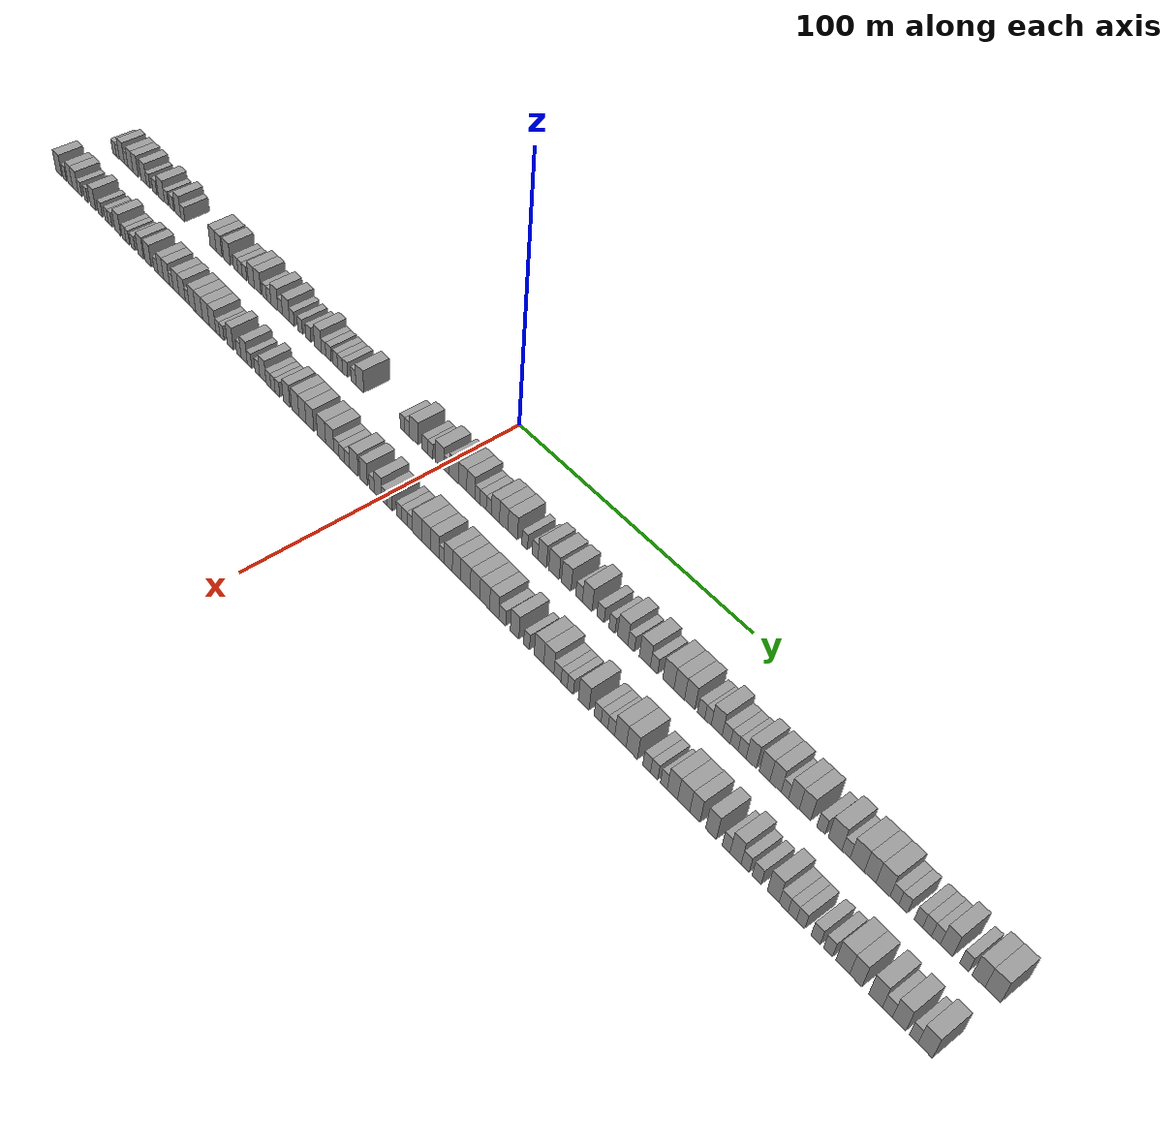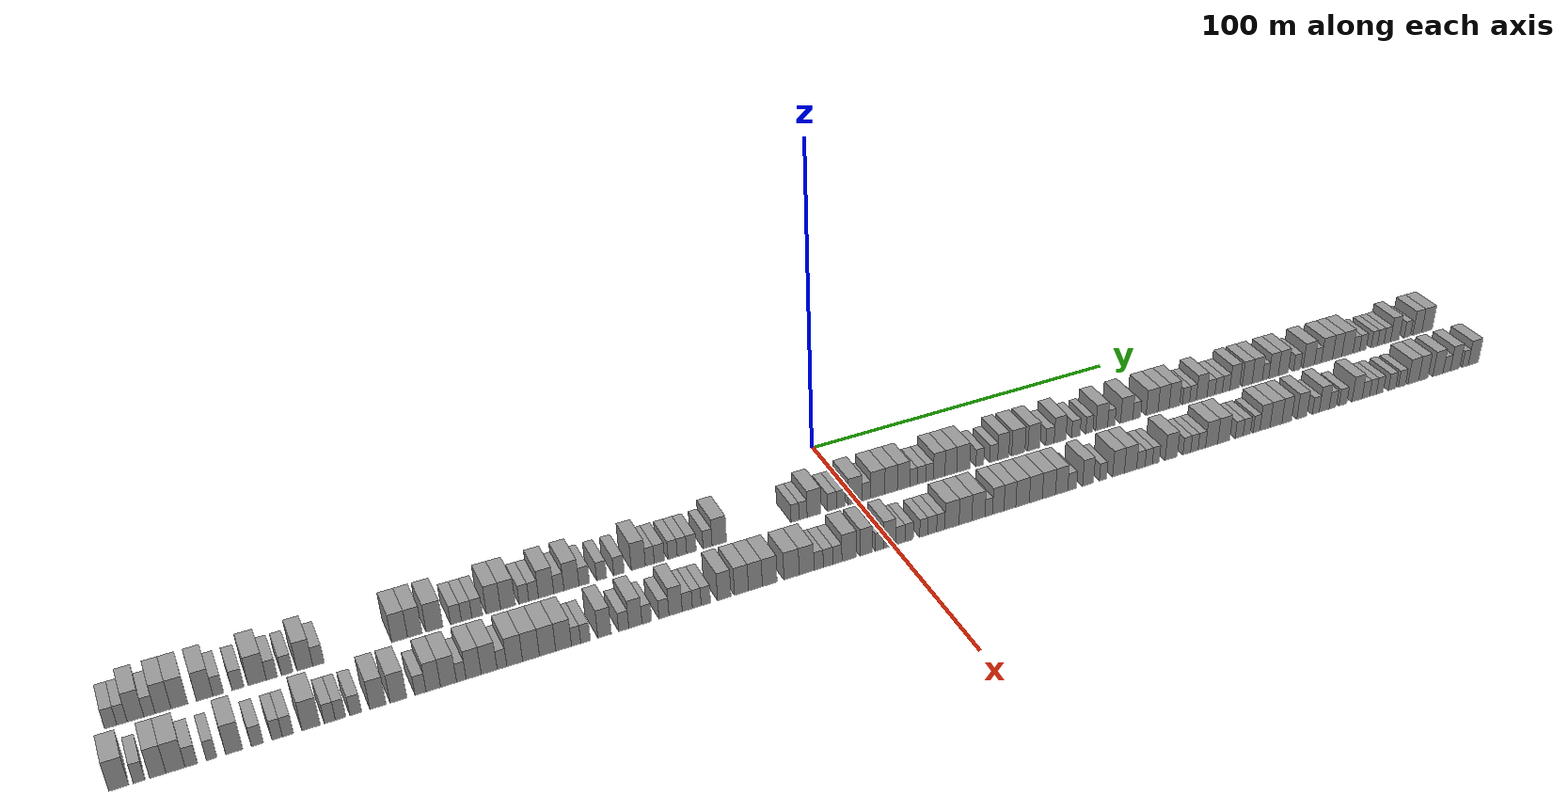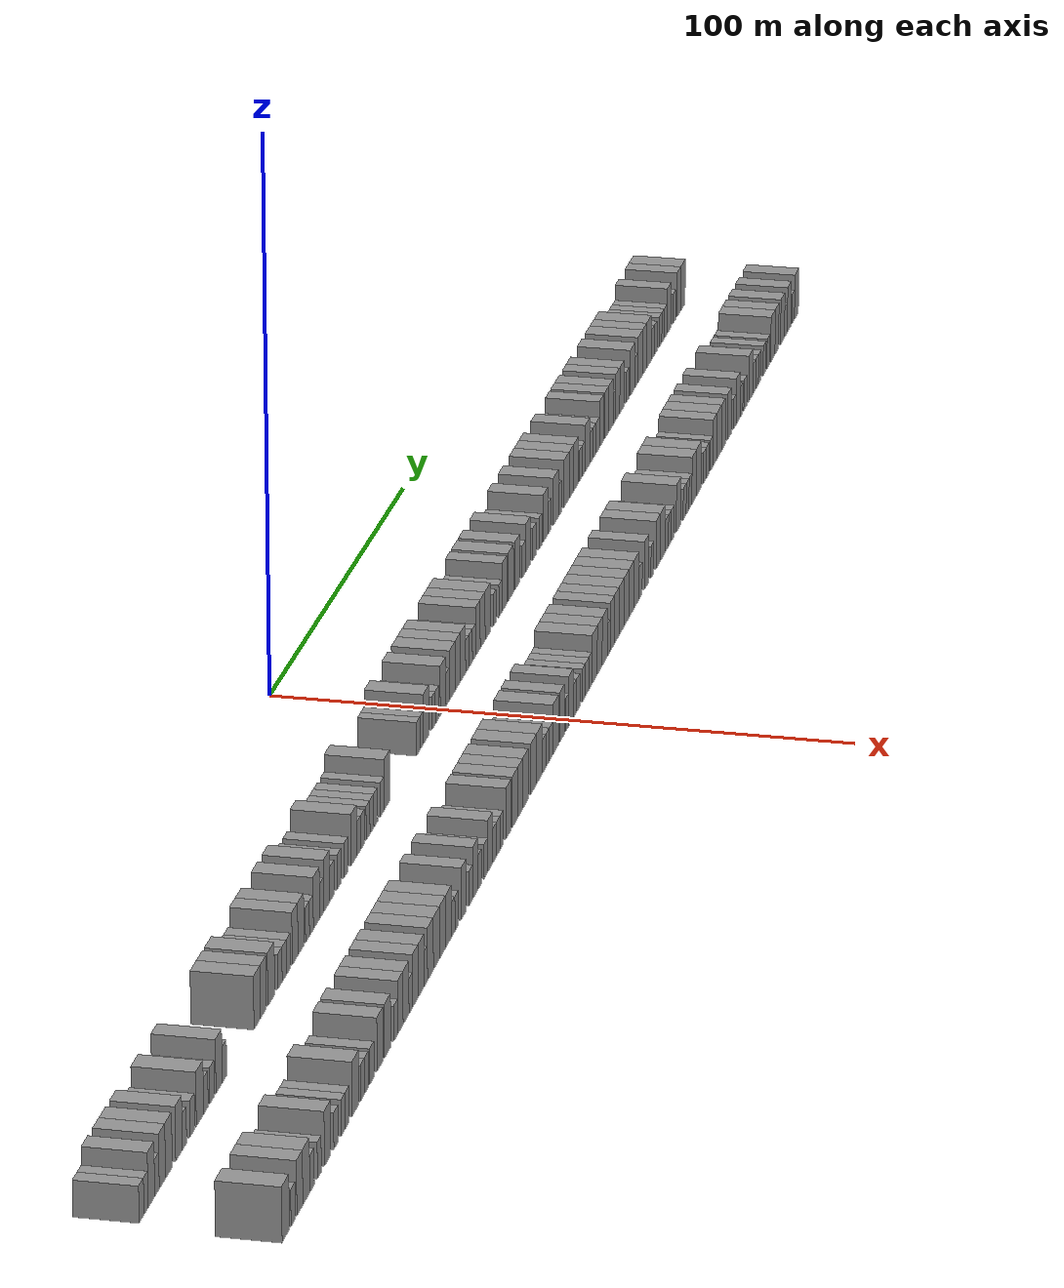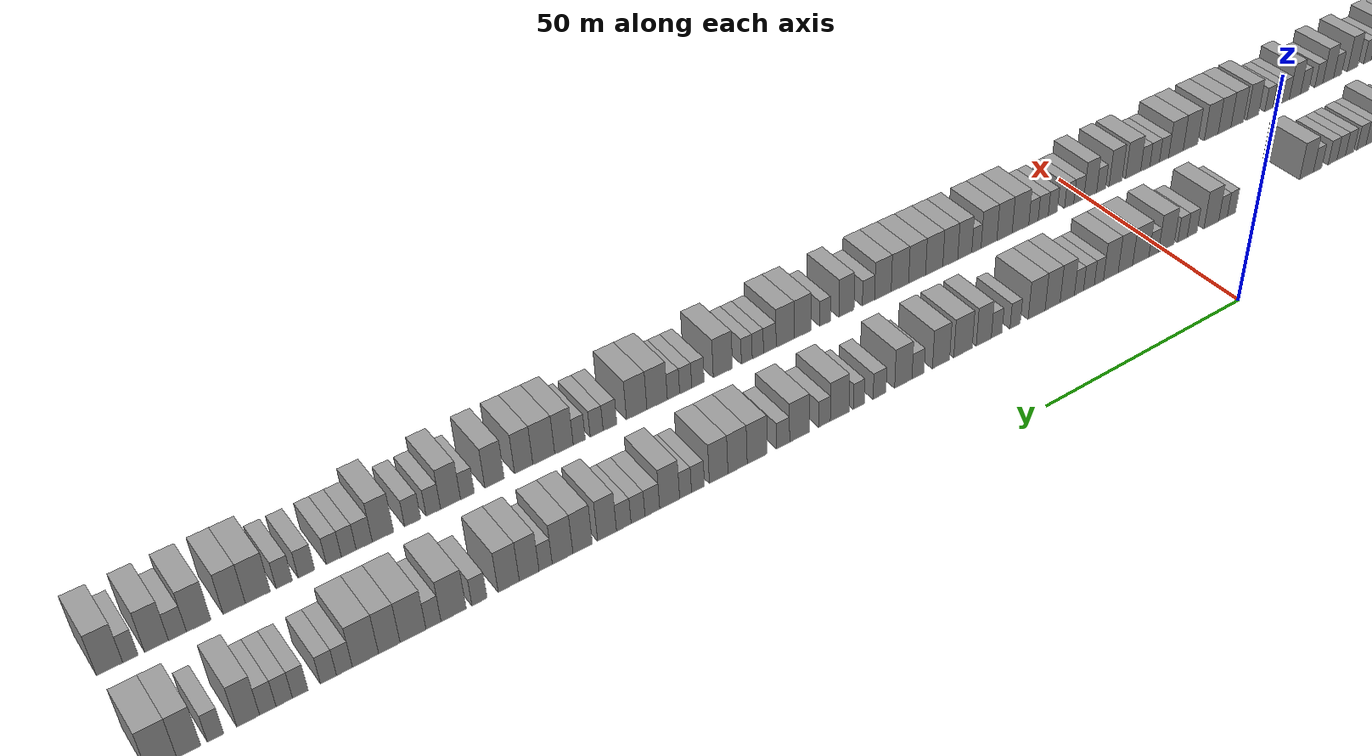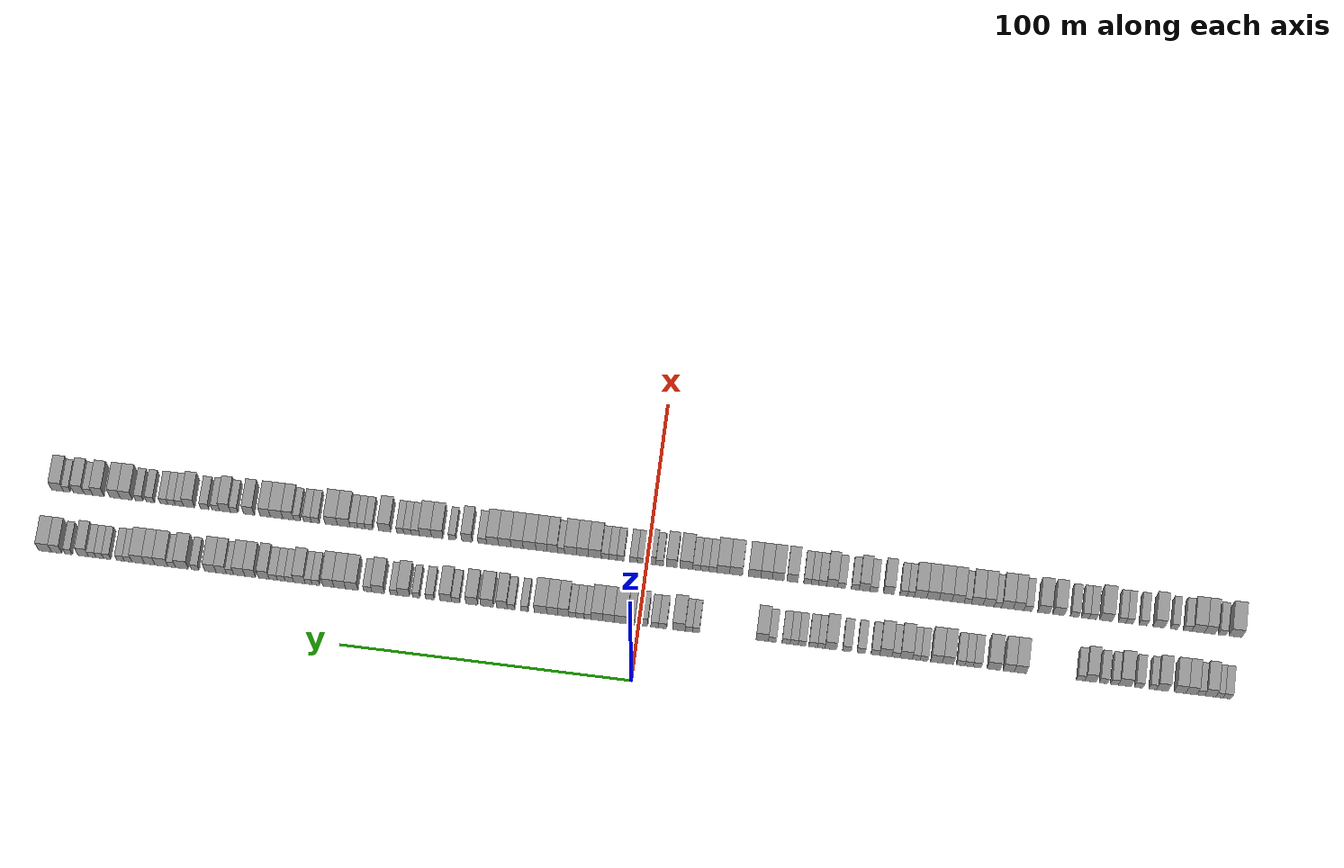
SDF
<sdf version="1.6">
 <world name="default">
  <scene>
   <sky><clouds><speed>12</speed></clouds></sky>
   <ambient>0.4 0.4 0.4 1</ambient>
   <background>0.7 0.7 0.7 1</background>
   <shadows>1</shadows>
  </scene>
  <gravity>0 0 -9.8066</gravity>
  <magnetic_field>6e-06 2.3e-05 -4.2e-05</magnetic_field>
  <physics default="0" name="default_physics" type="ode">
   <ode>
    <solver>
     <type>quick</type>
     <iters>10</iters>
     <sor>1.0</sor>
     <use_dynamic_moi_rescaling>0</use_dynamic_moi_rescaling>
    </solver>
    <constraints>
     <cfm>0</cfm>
     <erp>0.2</erp>
     <contact_max_correcting_vel>100</contact_max_correcting_vel>
     <contact_surface_layer>0.001</contact_surface_layer>
    </constraints>
   </ode>
   <max_step_size>0.004</max_step_size>
   <real_time_factor>1</real_time_factor>
   <real_time_update_rate>250</real_time_update_rate>
  </physics>
  <light name="sun" type="directional">
   <pose>0 0 10 0 0 0</pose>
   <diffuse>0.8 0.8 0.8 1</diffuse>
   <specular>0.2 0.2 0.2 1</specular>
   <attenuation>
    <range>1000</range>
    <constant>0.9</constant>
    <linear>0.01</linear>
    <quadratic>0.001</quadratic>
   </attenuation>
   <direction>-0.5 0.1 -0.9</direction>
  </light>
  <model name="building_1">
   <static>1</static>
   <pose>25.0000 -200.5957 0 0.000000 0.000000 0.000000</pose>
   <link name="link">
    <pose>0 0 3.00 0 0 0</pose>
    <collision name="collision"><geometry><box><size>10.0000 2.8085 6.0000</size></box></geometry></collision>
    <visual name="visual">
     <cast_shadows>0</cast_shadows>
     <geometry><box><size>10.0000 2.8085 6.0000</size></box></geometry>
     <material>
      <script>
       <uri>model://grey_wall/materials/scripts</uri>
       <uri>model://grey_wall/materials/textures</uri>
       <name>vrc/grey_wall</name>
      </script>
     </material>
    </visual>
   </link>
  </model>
  <model name="building_2">
   <static>1</static>
   <pose>25.0000 -197.9848 0 0.000000 0.000000 0.000000</pose>
   <link name="link">
    <pose>0 0 3.00 0 0 0</pose>
    <collision name="collision"><geometry><box><size>10.0000 2.4134 6.0000</size></box></geometry></collision>
    <visual name="visual">
     <cast_shadows>0</cast_shadows>
     <geometry><box><size>10.0000 2.4134 6.0000</size></box></geometry>
     <material>
      <script>
       <uri>model://grey_wall/materials/scripts</uri>
       <uri>model://grey_wall/materials/textures</uri>
       <name>vrc/grey_wall</name>
      </script>
     </material>
    </visual>
   </link>
  </model>
  <model name="building_3">
   <static>1</static>
   <pose>25.0000 -194.8523 0 0.000000 0.000000 0.000000</pose>
   <link name="link">
    <pose>0 0 4.50 0 0 0</pose>
    <collision name="collision"><geometry><box><size>10.0000 3.8517 9.0000</size></box></geometry></collision>
    <visual name="visual">
     <cast_shadows>0</cast_shadows>
     <geometry><box><size>10.0000 3.8517 9.0000</size></box></geometry>
     <material>
      <script>
       <uri>model://grey_wall/materials/scripts</uri>
       <uri>model://grey_wall/materials/textures</uri>
       <name>vrc/grey_wall</name>
      </script>
     </material>
    </visual>
   </link>
  </model>
  <model name="building_4">
   <static>1</static>
   <pose>25.0000 -191.6137 0 0.000000 0.000000 0.000000</pose>
   <link name="link">
    <pose>0 0 3.00 0 0 0</pose>
    <collision name="collision"><geometry><box><size>10.0000 2.6255 6.0000</size></box></geometry></collision>
    <visual name="visual">
     <cast_shadows>0</cast_shadows>
     <geometry><box><size>10.0000 2.6255 6.0000</size></box></geometry>
     <material>
      <script>
       <uri>model://grey_wall/materials/scripts</uri>
       <uri>model://grey_wall/materials/textures</uri>
       <name>vrc/grey_wall</name>
      </script>
     </material>
    </visual>
   </link>
  </model>
  <model name="building_5">
   <static>1</static>
   <pose>25.0000 -188.4409 0 0.000000 0.000000 0.000000</pose>
   <link name="link">
    <pose>0 0 4.50 0 0 0</pose>
    <collision name="collision"><geometry><box><size>10.0000 3.7200 9.0000</size></box></geometry></collision>
    <visual name="visual">
     <cast_shadows>0</cast_shadows>
     <geometry><box><size>10.0000 3.7200 9.0000</size></box></geometry>
     <material>
      <script>
       <uri>model://grey_wall/materials/scripts</uri>
       <uri>model://grey_wall/materials/textures</uri>
       <name>vrc/grey_wall</name>
      </script>
     </material>
    </visual>
   </link>
  </model>
  <model name="building_6">
   <static>1</static>
   <pose>25.0000 -184.5921 0 0.000000 0.000000 0.000000</pose>
   <link name="link">
    <pose>0 0 4.50 0 0 0</pose>
    <collision name="collision"><geometry><box><size>10.0000 3.9776 9.0000</size></box></geometry></collision>
    <visual name="visual">
     <cast_shadows>0</cast_shadows>
     <geometry><box><size>10.0000 3.9776 9.0000</size></box></geometry>
     <material>
      <script>
       <uri>model://grey_wall/materials/scripts</uri>
       <uri>model://grey_wall/materials/textures</uri>
       <name>vrc/grey_wall</name>
      </script>
     </material>
    </visual>
   </link>
  </model>
  <model name="building_7">
   <static>1</static>
   <pose>25.0000 -178.6157 0 0.000000 0.000000 0.000000</pose>
   <link name="link">
    <pose>0 0 4.50 0 0 0</pose>
    <collision name="collision"><geometry><box><size>10.0000 3.9752 9.0000</size></box></geometry></collision>
    <visual name="visual">
     <cast_shadows>0</cast_shadows>
     <geometry><box><size>10.0000 3.9752 9.0000</size></box></geometry>
     <material>
      <script>
       <uri>model://grey_wall/materials/scripts</uri>
       <uri>model://grey_wall/materials/textures</uri>
       <name>vrc/grey_wall</name>
      </script>
     </material>
    </visual>
   </link>
  </model>
  <model name="building_8">
   <static>1</static>
   <pose>25.0000 -175.3538 0 0.000000 0.000000 0.000000</pose>
   <link name="link">
    <pose>0 0 3.00 0 0 0</pose>
    <collision name="collision"><geometry><box><size>10.0000 2.5488 6.0000</size></box></geometry></collision>
    <visual name="visual">
     <cast_shadows>0</cast_shadows>
     <geometry><box><size>10.0000 2.5488 6.0000</size></box></geometry>
     <material>
      <script>
       <uri>model://grey_wall/materials/scripts</uri>
       <uri>model://grey_wall/materials/textures</uri>
       <name>vrc/grey_wall</name>
      </script>
     </material>
    </visual>
   </link>
  </model>
  <model name="building_9">
   <static>1</static>
   <pose>25.0000 -170.6239 0 0.000000 0.000000 0.000000</pose>
   <link name="link">
    <pose>0 0 3.00 0 0 0</pose>
    <collision name="collision"><geometry><box><size>10.0000 2.9109 6.0000</size></box></geometry></collision>
    <visual name="visual">
     <cast_shadows>0</cast_shadows>
     <geometry><box><size>10.0000 2.9109 6.0000</size></box></geometry>
     <material>
      <script>
       <uri>model://grey_wall/materials/scripts</uri>
       <uri>model://grey_wall/materials/textures</uri>
       <name>vrc/grey_wall</name>
      </script>
     </material>
    </visual>
   </link>
  </model>
  <model name="building_10">
   <static>1</static>
   <pose>25.0000 -165.9567 0 0.000000 0.000000 0.000000</pose>
   <link name="link">
    <pose>0 0 4.50 0 0 0</pose>
    <collision name="collision"><geometry><box><size>10.0000 4.4236 9.0000</size></box></geometry></collision>
    <visual name="visual">
     <cast_shadows>0</cast_shadows>
     <geometry><box><size>10.0000 4.4236 9.0000</size></box></geometry>
     <material>
      <script>
       <uri>model://grey_wall/materials/scripts</uri>
       <uri>model://grey_wall/materials/textures</uri>
       <name>vrc/grey_wall</name>
      </script>
     </material>
    </visual>
   </link>
  </model>
  <model name="building_11">
   <static>1</static>
   <pose>25.0000 -162.3852 0 0.000000 0.000000 0.000000</pose>
   <link name="link">
    <pose>0 0 3.00 0 0 0</pose>
    <collision name="collision"><geometry><box><size>10.0000 2.7193 6.0000</size></box></geometry></collision>
    <visual name="visual">
     <cast_shadows>0</cast_shadows>
     <geometry><box><size>10.0000 2.7193 6.0000</size></box></geometry>
     <material>
      <script>
       <uri>model://grey_wall/materials/scripts</uri>
       <uri>model://grey_wall/materials/textures</uri>
       <name>vrc/grey_wall</name>
      </script>
     </material>
    </visual>
   </link>
  </model>
  <model name="building_12">
   <static>1</static>
   <pose>25.0000 -158.6169 0 0.000000 0.000000 0.000000</pose>
   <link name="link">
    <pose>0 0 3.00 0 0 0</pose>
    <collision name="collision"><geometry><box><size>10.0000 2.8173 6.0000</size></box></geometry></collision>
    <visual name="visual">
     <cast_shadows>0</cast_shadows>
     <geometry><box><size>10.0000 2.8173 6.0000</size></box></geometry>
     <material>
      <script>
       <uri>model://grey_wall/materials/scripts</uri>
       <uri>model://grey_wall/materials/textures</uri>
       <name>vrc/grey_wall</name>
      </script>
     </material>
    </visual>
   </link>
  </model>
  <model name="building_13">
   <static>1</static>
   <pose>25.0000 -154.2598 0 0.000000 0.000000 0.000000</pose>
   <link name="link">
    <pose>0 0 4.50 0 0 0</pose>
    <collision name="collision"><geometry><box><size>10.0000 3.8968 9.0000</size></box></geometry></collision>
    <visual name="visual">
     <cast_shadows>0</cast_shadows>
     <geometry><box><size>10.0000 3.8968 9.0000</size></box></geometry>
     <material>
      <script>
       <uri>model://grey_wall/materials/scripts</uri>
       <uri>model://grey_wall/materials/textures</uri>
       <name>vrc/grey_wall</name>
      </script>
     </material>
    </visual>
   </link>
  </model>
  <model name="building_14">
   <static>1</static>
   <pose>25.0000 -150.8935 0 0.000000 0.000000 0.000000</pose>
   <link name="link">
    <pose>0 0 3.00 0 0 0</pose>
    <collision name="collision"><geometry><box><size>10.0000 2.8358 6.0000</size></box></geometry></collision>
    <visual name="visual">
     <cast_shadows>0</cast_shadows>
     <geometry><box><size>10.0000 2.8358 6.0000</size></box></geometry>
     <material>
      <script>
       <uri>model://grey_wall/materials/scripts</uri>
       <uri>model://grey_wall/materials/textures</uri>
       <name>vrc/grey_wall</name>
      </script>
     </material>
    </visual>
   </link>
  </model>
  <model name="building_15">
   <static>1</static>
   <pose>25.0000 -130.3425 0 0.000000 0.000000 0.000000</pose>
   <link name="link">
    <pose>0 0 4.50 0 0 0</pose>
    <collision name="collision"><geometry><box><size>10.0000 4.0888 9.0000</size></box></geometry></collision>
    <visual name="visual">
     <cast_shadows>0</cast_shadows>
     <geometry><box><size>10.0000 4.0888 9.0000</size></box></geometry>
     <material>
      <script>
       <uri>model://grey_wall/materials/scripts</uri>
       <uri>model://grey_wall/materials/textures</uri>
       <name>vrc/grey_wall</name>
      </script>
     </material>
    </visual>
   </link>
  </model>
  <model name="building_16">
   <static>1</static>
   <pose>25.0000 -126.3942 0 0.000000 0.000000 0.000000</pose>
   <link name="link">
    <pose>0 0 4.50 0 0 0</pose>
    <collision name="collision"><geometry><box><size>10.0000 3.8078 9.0000</size></box></geometry></collision>
    <visual name="visual">
     <cast_shadows>0</cast_shadows>
     <geometry><box><size>10.0000 3.8078 9.0000</size></box></geometry>
     <material>
      <script>
       <uri>model://grey_wall/materials/scripts</uri>
       <uri>model://grey_wall/materials/textures</uri>
       <name>vrc/grey_wall</name>
      </script>
     </material>
    </visual>
   </link>
  </model>
  <model name="building_17">
   <static>1</static>
   <pose>25.0000 -121.2702 0 0.000000 0.000000 0.000000</pose>
   <link name="link">
    <pose>0 0 4.50 0 0 0</pose>
    <collision name="collision"><geometry><box><size>10.0000 4.4401 9.0000</size></box></geometry></collision>
    <visual name="visual">
     <cast_shadows>0</cast_shadows>
     <geometry><box><size>10.0000 4.4401 9.0000</size></box></geometry>
     <material>
      <script>
       <uri>model://grey_wall/materials/scripts</uri>
       <uri>model://grey_wall/materials/textures</uri>
       <name>vrc/grey_wall</name>
      </script>
     </material>
    </visual>
   </link>
  </model>
  <model name="building_18">
   <static>1</static>
   <pose>25.0000 -115.6292 0 0.000000 0.000000 0.000000</pose>
   <link name="link">
    <pose>0 0 3.00 0 0 0</pose>
    <collision name="collision"><geometry><box><size>10.0000 2.8419 6.0000</size></box></geometry></collision>
    <visual name="visual">
     <cast_shadows>0</cast_shadows>
     <geometry><box><size>10.0000 2.8419 6.0000</size></box></geometry>
     <material>
      <script>
       <uri>model://grey_wall/materials/scripts</uri>
       <uri>model://grey_wall/materials/textures</uri>
       <name>vrc/grey_wall</name>
      </script>
     </material>
    </visual>
   </link>
  </model>
  <model name="building_19">
   <static>1</static>
   <pose>25.0000 -112.8165 0 0.000000 0.000000 0.000000</pose>
   <link name="link">
    <pose>0 0 3.00 0 0 0</pose>
    <collision name="collision"><geometry><box><size>10.0000 2.7835 6.0000</size></box></geometry></collision>
    <visual name="visual">
     <cast_shadows>0</cast_shadows>
     <geometry><box><size>10.0000 2.7835 6.0000</size></box></geometry>
     <material>
      <script>
       <uri>model://grey_wall/materials/scripts</uri>
       <uri>model://grey_wall/materials/textures</uri>
       <name>vrc/grey_wall</name>
      </script>
     </material>
    </visual>
   </link>
  </model>
  <model name="building_20">
   <static>1</static>
   <pose>25.0000 -110.0008 0 0.000000 0.000000 0.000000</pose>
   <link name="link">
    <pose>0 0 3.00 0 0 0</pose>
    <collision name="collision"><geometry><box><size>10.0000 2.8480 6.0000</size></box></geometry></collision>
    <visual name="visual">
     <cast_shadows>0</cast_shadows>
     <geometry><box><size>10.0000 2.8480 6.0000</size></box></geometry>
     <material>
      <script>
       <uri>model://grey_wall/materials/scripts</uri>
       <uri>model://grey_wall/materials/textures</uri>
       <name>vrc/grey_wall</name>
      </script>
     </material>
    </visual>
   </link>
  </model>
  <model name="building_21">
   <static>1</static>
   <pose>25.0000 -105.6616 0 0.000000 0.000000 0.000000</pose>
   <link name="link">
    <pose>0 0 4.50 0 0 0</pose>
    <collision name="collision"><geometry><box><size>10.0000 3.8304 9.0000</size></box></geometry></collision>
    <visual name="visual">
     <cast_shadows>0</cast_shadows>
     <geometry><box><size>10.0000 3.8304 9.0000</size></box></geometry>
     <material>
      <script>
       <uri>model://grey_wall/materials/scripts</uri>
       <uri>model://grey_wall/materials/textures</uri>
       <name>vrc/grey_wall</name>
      </script>
     </material>
    </visual>
   </link>
  </model>
  <model name="building_22">
   <static>1</static>
   <pose>25.0000 -101.7530 0 0.000000 0.000000 0.000000</pose>
   <link name="link">
    <pose>0 0 4.50 0 0 0</pose>
    <collision name="collision"><geometry><box><size>10.0000 3.9868 9.0000</size></box></geometry></collision>
    <visual name="visual">
     <cast_shadows>0</cast_shadows>
     <geometry><box><size>10.0000 3.9868 9.0000</size></box></geometry>
     <material>
      <script>
       <uri>model://grey_wall/materials/scripts</uri>
       <uri>model://grey_wall/materials/textures</uri>
       <name>vrc/grey_wall</name>
      </script>
     </material>
    </visual>
   </link>
  </model>
  <model name="building_23">
   <static>1</static>
   <pose>25.0000 -97.4480 0 0.000000 0.000000 0.000000</pose>
   <link name="link">
    <pose>0 0 3.00 0 0 0</pose>
    <collision name="collision"><geometry><box><size>10.0000 2.6234 6.0000</size></box></geometry></collision>
    <visual name="visual">
     <cast_shadows>0</cast_shadows>
     <geometry><box><size>10.0000 2.6234 6.0000</size></box></geometry>
     <material>
      <script>
       <uri>model://grey_wall/materials/scripts</uri>
       <uri>model://grey_wall/materials/textures</uri>
       <name>vrc/grey_wall</name>
      </script>
     </material>
    </visual>
   </link>
  </model>
  <model name="building_24">
   <static>1</static>
   <pose>25.0000 -94.8192 0 0.000000 0.000000 0.000000</pose>
   <link name="link">
    <pose>0 0 3.00 0 0 0</pose>
    <collision name="collision"><geometry><box><size>10.0000 2.6342 6.0000</size></box></geometry></collision>
    <visual name="visual">
     <cast_shadows>0</cast_shadows>
     <geometry><box><size>10.0000 2.6342 6.0000</size></box></geometry>
     <material>
      <script>
       <uri>model://grey_wall/materials/scripts</uri>
       <uri>model://grey_wall/materials/textures</uri>
       <name>vrc/grey_wall</name>
      </script>
     </material>
    </visual>
   </link>
  </model>
  <model name="building_25">
   <static>1</static>
   <pose>25.0000 -91.3993 0 0.000000 0.000000 0.000000</pose>
   <link name="link">
    <pose>0 0 4.50 0 0 0</pose>
    <collision name="collision"><geometry><box><size>10.0000 4.2055 9.0000</size></box></geometry></collision>
    <visual name="visual">
     <cast_shadows>0</cast_shadows>
     <geometry><box><size>10.0000 4.2055 9.0000</size></box></geometry>
     <material>
      <script>
       <uri>model://grey_wall/materials/scripts</uri>
       <uri>model://grey_wall/materials/textures</uri>
       <name>vrc/grey_wall</name>
      </script>
     </material>
    </visual>
   </link>
  </model>
  <model name="building_26">
   <static>1</static>
   <pose>25.0000 -87.9068 0 0.000000 0.000000 0.000000</pose>
   <link name="link">
    <pose>0 0 3.00 0 0 0</pose>
    <collision name="collision"><geometry><box><size>10.0000 2.7796 6.0000</size></box></geometry></collision>
    <visual name="visual">
     <cast_shadows>0</cast_shadows>
     <geometry><box><size>10.0000 2.7796 6.0000</size></box></geometry>
     <material>
      <script>
       <uri>model://grey_wall/materials/scripts</uri>
       <uri>model://grey_wall/materials/textures</uri>
       <name>vrc/grey_wall</name>
      </script>
     </material>
    </visual>
   </link>
  </model>
  <model name="building_27">
   <static>1</static>
   <pose>25.0000 -84.4294 0 0.000000 0.000000 0.000000</pose>
   <link name="link">
    <pose>0 0 4.50 0 0 0</pose>
    <collision name="collision"><geometry><box><size>10.0000 4.1752 9.0000</size></box></geometry></collision>
    <visual name="visual">
     <cast_shadows>0</cast_shadows>
     <geometry><box><size>10.0000 4.1752 9.0000</size></box></geometry>
     <material>
      <script>
       <uri>model://grey_wall/materials/scripts</uri>
       <uri>model://grey_wall/materials/textures</uri>
       <name>vrc/grey_wall</name>
      </script>
     </material>
    </visual>
   </link>
  </model>
  <model name="building_28">
   <static>1</static>
   <pose>25.0000 -80.8772 0 0.000000 0.000000 0.000000</pose>
   <link name="link">
    <pose>0 0 3.00 0 0 0</pose>
    <collision name="collision"><geometry><box><size>10.0000 2.9291 6.0000</size></box></geometry></collision>
    <visual name="visual">
     <cast_shadows>0</cast_shadows>
     <geometry><box><size>10.0000 2.9291 6.0000</size></box></geometry>
     <material>
      <script>
       <uri>model://grey_wall/materials/scripts</uri>
       <uri>model://grey_wall/materials/textures</uri>
       <name>vrc/grey_wall</name>
      </script>
     </material>
    </visual>
   </link>
  </model>
  <model name="building_29">
   <static>1</static>
   <pose>25.0000 -76.0206 0 0.000000 0.000000 0.000000</pose>
   <link name="link">
    <pose>0 0 3.00 0 0 0</pose>
    <collision name="collision"><geometry><box><size>10.0000 2.7842 6.0000</size></box></geometry></collision>
    <visual name="visual">
     <cast_shadows>0</cast_shadows>
     <geometry><box><size>10.0000 2.7842 6.0000</size></box></geometry>
     <material>
      <script>
       <uri>model://grey_wall/materials/scripts</uri>
       <uri>model://grey_wall/materials/textures</uri>
       <name>vrc/grey_wall</name>
      </script>
     </material>
    </visual>
   </link>
  </model>
  <model name="building_30">
   <static>1</static>
   <pose>25.0000 -71.1401 0 0.000000 0.000000 0.000000</pose>
   <link name="link">
    <pose>0 0 3.00 0 0 0</pose>
    <collision name="collision"><geometry><box><size>10.0000 2.9768 6.0000</size></box></geometry></collision>
    <visual name="visual">
     <cast_shadows>0</cast_shadows>
     <geometry><box><size>10.0000 2.9768 6.0000</size></box></geometry>
     <material>
      <script>
       <uri>model://grey_wall/materials/scripts</uri>
       <uri>model://grey_wall/materials/textures</uri>
       <name>vrc/grey_wall</name>
      </script>
     </material>
    </visual>
   </link>
  </model>
  <model name="building_31">
   <static>1</static>
   <pose>25.0000 -65.6525 0 0.000000 0.000000 0.000000</pose>
   <link name="link">
    <pose>0 0 4.50 0 0 0</pose>
    <collision name="collision"><geometry><box><size>10.0000 3.9983 9.0000</size></box></geometry></collision>
    <visual name="visual">
     <cast_shadows>0</cast_shadows>
     <geometry><box><size>10.0000 3.9983 9.0000</size></box></geometry>
     <material>
      <script>
       <uri>model://grey_wall/materials/scripts</uri>
       <uri>model://grey_wall/materials/textures</uri>
       <name>vrc/grey_wall</name>
      </script>
     </material>
    </visual>
   </link>
  </model>
  <model name="building_32">
   <static>1</static>
   <pose>25.0000 -62.3743 0 0.000000 0.000000 0.000000</pose>
   <link name="link">
    <pose>0 0 3.00 0 0 0</pose>
    <collision name="collision"><geometry><box><size>10.0000 2.5583 6.0000</size></box></geometry></collision>
    <visual name="visual">
     <cast_shadows>0</cast_shadows>
     <geometry><box><size>10.0000 2.5583 6.0000</size></box></geometry>
     <material>
      <script>
       <uri>model://grey_wall/materials/scripts</uri>
       <uri>model://grey_wall/materials/textures</uri>
       <name>vrc/grey_wall</name>
      </script>
     </material>
    </visual>
   </link>
  </model>
  <model name="building_33">
   <static>1</static>
   <pose>25.0000 -59.6118 0 0.000000 0.000000 0.000000</pose>
   <link name="link">
    <pose>0 0 3.00 0 0 0</pose>
    <collision name="collision"><geometry><box><size>10.0000 2.9667 6.0000</size></box></geometry></collision>
    <visual name="visual">
     <cast_shadows>0</cast_shadows>
     <geometry><box><size>10.0000 2.9667 6.0000</size></box></geometry>
     <material>
      <script>
       <uri>model://grey_wall/materials/scripts</uri>
       <uri>model://grey_wall/materials/textures</uri>
       <name>vrc/grey_wall</name>
      </script>
     </material>
    </visual>
   </link>
  </model>
  <model name="building_34">
   <static>1</static>
   <pose>25.0000 -55.7953 0 0.000000 0.000000 0.000000</pose>
   <link name="link">
    <pose>0 0 3.00 0 0 0</pose>
    <collision name="collision"><geometry><box><size>10.0000 2.6663 6.0000</size></box></geometry></collision>
    <visual name="visual">
     <cast_shadows>0</cast_shadows>
     <geometry><box><size>10.0000 2.6663 6.0000</size></box></geometry>
     <material>
      <script>
       <uri>model://grey_wall/materials/scripts</uri>
       <uri>model://grey_wall/materials/textures</uri>
       <name>vrc/grey_wall</name>
      </script>
     </material>
    </visual>
   </link>
  </model>
  <model name="building_35">
   <static>1</static>
   <pose>25.0000 -53.0980 0 0.000000 0.000000 0.000000</pose>
   <link name="link">
    <pose>0 0 3.00 0 0 0</pose>
    <collision name="collision"><geometry><box><size>10.0000 2.7282 6.0000</size></box></geometry></collision>
    <visual name="visual">
     <cast_shadows>0</cast_shadows>
     <geometry><box><size>10.0000 2.7282 6.0000</size></box></geometry>
     <material>
      <script>
       <uri>model://grey_wall/materials/scripts</uri>
       <uri>model://grey_wall/materials/textures</uri>
       <name>vrc/grey_wall</name>
      </script>
     </material>
    </visual>
   </link>
  </model>
  <model name="building_36">
   <static>1</static>
   <pose>25.0000 -50.3425 0 0.000000 0.000000 0.000000</pose>
   <link name="link">
    <pose>0 0 3.00 0 0 0</pose>
    <collision name="collision"><geometry><box><size>10.0000 2.7828 6.0000</size></box></geometry></collision>
    <visual name="visual">
     <cast_shadows>0</cast_shadows>
     <geometry><box><size>10.0000 2.7828 6.0000</size></box></geometry>
     <material>
      <script>
       <uri>model://grey_wall/materials/scripts</uri>
       <uri>model://grey_wall/materials/textures</uri>
       <name>vrc/grey_wall</name>
      </script>
     </material>
    </visual>
   </link>
  </model>
  <model name="building_37">
   <static>1</static>
   <pose>25.0000 -45.6284 0 0.000000 0.000000 0.000000</pose>
   <link name="link">
    <pose>0 0 3.00 0 0 0</pose>
    <collision name="collision"><geometry><box><size>10.0000 2.6455 6.0000</size></box></geometry></collision>
    <visual name="visual">
     <cast_shadows>0</cast_shadows>
     <geometry><box><size>10.0000 2.6455 6.0000</size></box></geometry>
     <material>
      <script>
       <uri>model://grey_wall/materials/scripts</uri>
       <uri>model://grey_wall/materials/textures</uri>
       <name>vrc/grey_wall</name>
      </script>
     </material>
    </visual>
   </link>
  </model>
  <model name="building_38">
   <static>1</static>
   <pose>25.0000 -42.1798 0 0.000000 0.000000 0.000000</pose>
   <link name="link">
    <pose>0 0 4.50 0 0 0</pose>
    <collision name="collision"><geometry><box><size>10.0000 4.2517 9.0000</size></box></geometry></collision>
    <visual name="visual">
     <cast_shadows>0</cast_shadows>
     <geometry><box><size>10.0000 4.2517 9.0000</size></box></geometry>
     <material>
      <script>
       <uri>model://grey_wall/materials/scripts</uri>
       <uri>model://grey_wall/materials/textures</uri>
       <name>vrc/grey_wall</name>
      </script>
     </material>
    </visual>
   </link>
  </model>
  <model name="building_39">
   <static>1</static>
   <pose>25.0000 -19.4496 0 0.000000 0.000000 0.000000</pose>
   <link name="link">
    <pose>0 0 3.00 0 0 0</pose>
    <collision name="collision"><geometry><box><size>10.0000 2.4029 6.0000</size></box></geometry></collision>
    <visual name="visual">
     <cast_shadows>0</cast_shadows>
     <geometry><box><size>10.0000 2.4029 6.0000</size></box></geometry>
     <material>
      <script>
       <uri>model://grey_wall/materials/scripts</uri>
       <uri>model://grey_wall/materials/textures</uri>
       <name>vrc/grey_wall</name>
      </script>
     </material>
    </visual>
   </link>
  </model>
  <model name="building_40">
   <static>1</static>
   <pose>25.0000 -16.9956 0 0.000000 0.000000 0.000000</pose>
   <link name="link">
    <pose>0 0 3.00 0 0 0</pose>
    <collision name="collision"><geometry><box><size>10.0000 2.5051 6.0000</size></box></geometry></collision>
    <visual name="visual">
     <cast_shadows>0</cast_shadows>
     <geometry><box><size>10.0000 2.5051 6.0000</size></box></geometry>
     <material>
      <script>
       <uri>model://grey_wall/materials/scripts</uri>
       <uri>model://grey_wall/materials/textures</uri>
       <name>vrc/grey_wall</name>
      </script>
     </material>
    </visual>
   </link>
  </model>
  <model name="building_41">
   <static>1</static>
   <pose>25.0000 -13.5917 0 0.000000 0.000000 0.000000</pose>
   <link name="link">
    <pose>0 0 4.50 0 0 0</pose>
    <collision name="collision"><geometry><box><size>10.0000 4.3028 9.0000</size></box></geometry></collision>
    <visual name="visual">
     <cast_shadows>0</cast_shadows>
     <geometry><box><size>10.0000 4.3028 9.0000</size></box></geometry>
     <material>
      <script>
       <uri>model://grey_wall/materials/scripts</uri>
       <uri>model://grey_wall/materials/textures</uri>
       <name>vrc/grey_wall</name>
      </script>
     </material>
    </visual>
   </link>
  </model>
  <model name="building_42">
   <static>1</static>
   <pose>25.0000 -8.0424 0 0.000000 0.000000 0.000000</pose>
   <link name="link">
    <pose>0 0 3.00 0 0 0</pose>
    <collision name="collision"><geometry><box><size>10.0000 2.7958 6.0000</size></box></geometry></collision>
    <visual name="visual">
     <cast_shadows>0</cast_shadows>
     <geometry><box><size>10.0000 2.7958 6.0000</size></box></geometry>
     <material>
      <script>
       <uri>model://grey_wall/materials/scripts</uri>
       <uri>model://grey_wall/materials/textures</uri>
       <name>vrc/grey_wall</name>
      </script>
     </material>
    </visual>
   </link>
  </model>
  <model name="building_43">
   <static>1</static>
   <pose>25.0000 -5.2995 0 0.000000 0.000000 0.000000</pose>
   <link name="link">
    <pose>0 0 3.00 0 0 0</pose>
    <collision name="collision"><geometry><box><size>10.0000 2.6900 6.0000</size></box></geometry></collision>
    <visual name="visual">
     <cast_shadows>0</cast_shadows>
     <geometry><box><size>10.0000 2.6900 6.0000</size></box></geometry>
     <material>
      <script>
       <uri>model://grey_wall/materials/scripts</uri>
       <uri>model://grey_wall/materials/textures</uri>
       <name>vrc/grey_wall</name>
      </script>
     </material>
    </visual>
   </link>
  </model>
  <model name="building_44">
   <static>1</static>
   <pose>25.0000 -0.7623 0 0.000000 0.000000 0.000000</pose>
   <link name="link">
    <pose>0 0 4.50 0 0 0</pose>
    <collision name="collision"><geometry><box><size>10.0000 4.3845 9.0000</size></box></geometry></collision>
    <visual name="visual">
     <cast_shadows>0</cast_shadows>
     <geometry><box><size>10.0000 4.3845 9.0000</size></box></geometry>
     <material>
      <script>
       <uri>model://grey_wall/materials/scripts</uri>
       <uri>model://grey_wall/materials/textures</uri>
       <name>vrc/grey_wall</name>
      </script>
     </material>
    </visual>
   </link>
  </model>
  <model name="building_45">
   <static>1</static>
   <pose>25.0000 2.7781 0 0.000000 0.000000 0.000000</pose>
   <link name="link">
    <pose>0 0 3.00 0 0 0</pose>
    <collision name="collision"><geometry><box><size>10.0000 2.6963 6.0000</size></box></geometry></collision>
    <visual name="visual">
     <cast_shadows>0</cast_shadows>
     <geometry><box><size>10.0000 2.6963 6.0000</size></box></geometry>
     <material>
      <script>
       <uri>model://grey_wall/materials/scripts</uri>
       <uri>model://grey_wall/materials/textures</uri>
       <name>vrc/grey_wall</name>
      </script>
     </material>
    </visual>
   </link>
  </model>
  <model name="building_46">
   <static>1</static>
   <pose>25.0000 6.3581 0 0.000000 0.000000 0.000000</pose>
   <link name="link">
    <pose>0 0 4.50 0 0 0</pose>
    <collision name="collision"><geometry><box><size>10.0000 4.4637 9.0000</size></box></geometry></collision>
    <visual name="visual">
     <cast_shadows>0</cast_shadows>
     <geometry><box><size>10.0000 4.4637 9.0000</size></box></geometry>
     <material>
      <script>
       <uri>model://grey_wall/materials/scripts</uri>
       <uri>model://grey_wall/materials/textures</uri>
       <name>vrc/grey_wall</name>
      </script>
     </material>
    </visual>
   </link>
  </model>
  <model name="building_47">
   <static>1</static>
   <pose>25.0000 10.5509 0 0.000000 0.000000 0.000000</pose>
   <link name="link">
    <pose>0 0 4.50 0 0 0</pose>
    <collision name="collision"><geometry><box><size>10.0000 3.9219 9.0000</size></box></geometry></collision>
    <visual name="visual">
     <cast_shadows>0</cast_shadows>
     <geometry><box><size>10.0000 3.9219 9.0000</size></box></geometry>
     <material>
      <script>
       <uri>model://grey_wall/materials/scripts</uri>
       <uri>model://grey_wall/materials/textures</uri>
       <name>vrc/grey_wall</name>
      </script>
     </material>
    </visual>
   </link>
  </model>
  <model name="building_48">
   <static>1</static>
   <pose>25.0000 14.4988 0 0.000000 0.000000 0.000000</pose>
   <link name="link">
    <pose>0 0 4.50 0 0 0</pose>
    <collision name="collision"><geometry><box><size>10.0000 3.9739 9.0000</size></box></geometry></collision>
    <visual name="visual">
     <cast_shadows>0</cast_shadows>
     <geometry><box><size>10.0000 3.9739 9.0000</size></box></geometry>
     <material>
      <script>
       <uri>model://grey_wall/materials/scripts</uri>
       <uri>model://grey_wall/materials/textures</uri>
       <name>vrc/grey_wall</name>
      </script>
     </material>
    </visual>
   </link>
  </model>
  <model name="building_49">
   <static>1</static>
   <pose>25.0000 17.6950 0 0.000000 0.000000 0.000000</pose>
   <link name="link">
    <pose>0 0 3.00 0 0 0</pose>
    <collision name="collision"><geometry><box><size>10.0000 2.4185 6.0000</size></box></geometry></collision>
    <visual name="visual">
     <cast_shadows>0</cast_shadows>
     <geometry><box><size>10.0000 2.4185 6.0000</size></box></geometry>
     <material>
      <script>
       <uri>model://grey_wall/materials/scripts</uri>
       <uri>model://grey_wall/materials/textures</uri>
       <name>vrc/grey_wall</name>
      </script>
     </material>
    </visual>
   </link>
  </model>
  <model name="building_50">
   <static>1</static>
   <pose>25.0000 20.3509 0 0.000000 0.000000 0.000000</pose>
   <link name="link">
    <pose>0 0 3.00 0 0 0</pose>
    <collision name="collision"><geometry><box><size>10.0000 2.8933 6.0000</size></box></geometry></collision>
    <visual name="visual">
     <cast_shadows>0</cast_shadows>
     <geometry><box><size>10.0000 2.8933 6.0000</size></box></geometry>
     <material>
      <script>
       <uri>model://grey_wall/materials/scripts</uri>
       <uri>model://grey_wall/materials/textures</uri>
       <name>vrc/grey_wall</name>
      </script>
     </material>
    </visual>
   </link>
  </model>
  <model name="building_51">
   <static>1</static>
   <pose>25.0000 22.9984 0 0.000000 0.000000 0.000000</pose>
   <link name="link">
    <pose>0 0 3.00 0 0 0</pose>
    <collision name="collision"><geometry><box><size>10.0000 2.4018 6.0000</size></box></geometry></collision>
    <visual name="visual">
     <cast_shadows>0</cast_shadows>
     <geometry><box><size>10.0000 2.4018 6.0000</size></box></geometry>
     <material>
      <script>
       <uri>model://grey_wall/materials/scripts</uri>
       <uri>model://grey_wall/materials/textures</uri>
       <name>vrc/grey_wall</name>
      </script>
     </material>
    </visual>
   </link>
  </model>
  <model name="building_52">
   <static>1</static>
   <pose>25.0000 26.0617 0 0.000000 0.000000 0.000000</pose>
   <link name="link">
    <pose>0 0 4.50 0 0 0</pose>
    <collision name="collision"><geometry><box><size>10.0000 3.7248 9.0000</size></box></geometry></collision>
    <visual name="visual">
     <cast_shadows>0</cast_shadows>
     <geometry><box><size>10.0000 3.7248 9.0000</size></box></geometry>
     <material>
      <script>
       <uri>model://grey_wall/materials/scripts</uri>
       <uri>model://grey_wall/materials/textures</uri>
       <name>vrc/grey_wall</name>
      </script>
     </material>
    </visual>
   </link>
  </model>
  <model name="building_53">
   <static>1</static>
   <pose>25.0000 29.8570 0 0.000000 0.000000 0.000000</pose>
   <link name="link">
    <pose>0 0 4.50 0 0 0</pose>
    <collision name="collision"><geometry><box><size>10.0000 3.8659 9.0000</size></box></geometry></collision>
    <visual name="visual">
     <cast_shadows>0</cast_shadows>
     <geometry><box><size>10.0000 3.8659 9.0000</size></box></geometry>
     <material>
      <script>
       <uri>model://grey_wall/materials/scripts</uri>
       <uri>model://grey_wall/materials/textures</uri>
       <name>vrc/grey_wall</name>
      </script>
     </material>
    </visual>
   </link>
  </model>
  <model name="building_54">
   <static>1</static>
   <pose>25.0000 33.9565 0 0.000000 0.000000 0.000000</pose>
   <link name="link">
    <pose>0 0 4.50 0 0 0</pose>
    <collision name="collision"><geometry><box><size>10.0000 4.3330 9.0000</size></box></geometry></collision>
    <visual name="visual">
     <cast_shadows>0</cast_shadows>
     <geometry><box><size>10.0000 4.3330 9.0000</size></box></geometry>
     <material>
      <script>
       <uri>model://grey_wall/materials/scripts</uri>
       <uri>model://grey_wall/materials/textures</uri>
       <name>vrc/grey_wall</name>
      </script>
     </material>
    </visual>
   </link>
  </model>
  <model name="building_55">
   <static>1</static>
   <pose>25.0000 39.4166 0 0.000000 0.000000 0.000000</pose>
   <link name="link">
    <pose>0 0 3.00 0 0 0</pose>
    <collision name="collision"><geometry><box><size>10.0000 2.5872 6.0000</size></box></geometry></collision>
    <visual name="visual">
     <cast_shadows>0</cast_shadows>
     <geometry><box><size>10.0000 2.5872 6.0000</size></box></geometry>
     <material>
      <script>
       <uri>model://grey_wall/materials/scripts</uri>
       <uri>model://grey_wall/materials/textures</uri>
       <name>vrc/grey_wall</name>
      </script>
     </material>
    </visual>
   </link>
  </model>
  <model name="building_56">
   <static>1</static>
   <pose>25.0000 44.0428 0 0.000000 0.000000 0.000000</pose>
   <link name="link">
    <pose>0 0 3.00 0 0 0</pose>
    <collision name="collision"><geometry><box><size>10.0000 2.6652 6.0000</size></box></geometry></collision>
    <visual name="visual">
     <cast_shadows>0</cast_shadows>
     <geometry><box><size>10.0000 2.6652 6.0000</size></box></geometry>
     <material>
      <script>
       <uri>model://grey_wall/materials/scripts</uri>
       <uri>model://grey_wall/materials/textures</uri>
       <name>vrc/grey_wall</name>
      </script>
     </material>
    </visual>
   </link>
  </model>
  <model name="building_57">
   <static>1</static>
   <pose>25.0000 47.2270 0 0.000000 0.000000 0.000000</pose>
   <link name="link">
    <pose>0 0 4.50 0 0 0</pose>
    <collision name="collision"><geometry><box><size>10.0000 3.7030 9.0000</size></box></geometry></collision>
    <visual name="visual">
     <cast_shadows>0</cast_shadows>
     <geometry><box><size>10.0000 3.7030 9.0000</size></box></geometry>
     <material>
      <script>
       <uri>model://grey_wall/materials/scripts</uri>
       <uri>model://grey_wall/materials/textures</uri>
       <name>vrc/grey_wall</name>
      </script>
     </material>
    </visual>
   </link>
  </model>
  <model name="building_58">
   <static>1</static>
   <pose>25.0000 52.3160 0 0.000000 0.000000 0.000000</pose>
   <link name="link">
    <pose>0 0 4.50 0 0 0</pose>
    <collision name="collision"><geometry><box><size>10.0000 4.4752 9.0000</size></box></geometry></collision>
    <visual name="visual">
     <cast_shadows>0</cast_shadows>
     <geometry><box><size>10.0000 4.4752 9.0000</size></box></geometry>
     <material>
      <script>
       <uri>model://grey_wall/materials/scripts</uri>
       <uri>model://grey_wall/materials/textures</uri>
       <name>vrc/grey_wall</name>
      </script>
     </material>
    </visual>
   </link>
  </model>
  <model name="building_59">
   <static>1</static>
   <pose>25.0000 57.6080 0 0.000000 0.000000 0.000000</pose>
   <link name="link">
    <pose>0 0 4.50 0 0 0</pose>
    <collision name="collision"><geometry><box><size>10.0000 4.1088 9.0000</size></box></geometry></collision>
    <visual name="visual">
     <cast_shadows>0</cast_shadows>
     <geometry><box><size>10.0000 4.1088 9.0000</size></box></geometry>
     <material>
      <script>
       <uri>model://grey_wall/materials/scripts</uri>
       <uri>model://grey_wall/materials/textures</uri>
       <name>vrc/grey_wall</name>
      </script>
     </material>
    </visual>
   </link>
  </model>
  <model name="building_60">
   <static>1</static>
   <pose>25.0000 63.0838 0 0.000000 0.000000 0.000000</pose>
   <link name="link">
    <pose>0 0 3.00 0 0 0</pose>
    <collision name="collision"><geometry><box><size>10.0000 2.8429 6.0000</size></box></geometry></collision>
    <visual name="visual">
     <cast_shadows>0</cast_shadows>
     <geometry><box><size>10.0000 2.8429 6.0000</size></box></geometry>
     <material>
      <script>
       <uri>model://grey_wall/materials/scripts</uri>
       <uri>model://grey_wall/materials/textures</uri>
       <name>vrc/grey_wall</name>
      </script>
     </material>
    </visual>
   </link>
  </model>
  <model name="building_61">
   <static>1</static>
   <pose>25.0000 66.5258 0 0.000000 0.000000 0.000000</pose>
   <link name="link">
    <pose>0 0 4.50 0 0 0</pose>
    <collision name="collision"><geometry><box><size>10.0000 4.0410 9.0000</size></box></geometry></collision>
    <visual name="visual">
     <cast_shadows>0</cast_shadows>
     <geometry><box><size>10.0000 4.0410 9.0000</size></box></geometry>
     <material>
      <script>
       <uri>model://grey_wall/materials/scripts</uri>
       <uri>model://grey_wall/materials/textures</uri>
       <name>vrc/grey_wall</name>
      </script>
     </material>
    </visual>
   </link>
  </model>
  <model name="building_62">
   <static>1</static>
   <pose>25.0000 72.0242 0 0.000000 0.000000 0.000000</pose>
   <link name="link">
    <pose>0 0 3.00 0 0 0</pose>
    <collision name="collision"><geometry><box><size>10.0000 2.9557 6.0000</size></box></geometry></collision>
    <visual name="visual">
     <cast_shadows>0</cast_shadows>
     <geometry><box><size>10.0000 2.9557 6.0000</size></box></geometry>
     <material>
      <script>
       <uri>model://grey_wall/materials/scripts</uri>
       <uri>model://grey_wall/materials/textures</uri>
       <name>vrc/grey_wall</name>
      </script>
     </material>
    </visual>
   </link>
  </model>
  <model name="building_63">
   <static>1</static>
   <pose>25.0000 76.7353 0 0.000000 0.000000 0.000000</pose>
   <link name="link">
    <pose>0 0 3.00 0 0 0</pose>
    <collision name="collision"><geometry><box><size>10.0000 2.4665 6.0000</size></box></geometry></collision>
    <visual name="visual">
     <cast_shadows>0</cast_shadows>
     <geometry><box><size>10.0000 2.4665 6.0000</size></box></geometry>
     <material>
      <script>
       <uri>model://grey_wall/materials/scripts</uri>
       <uri>model://grey_wall/materials/textures</uri>
       <name>vrc/grey_wall</name>
      </script>
     </material>
    </visual>
   </link>
  </model>
  <model name="building_64">
   <static>1</static>
   <pose>25.0000 81.0686 0 0.000000 0.000000 0.000000</pose>
   <link name="link">
    <pose>0 0 4.50 0 0 0</pose>
    <collision name="collision"><geometry><box><size>10.0000 4.2000 9.0000</size></box></geometry></collision>
    <visual name="visual">
     <cast_shadows>0</cast_shadows>
     <geometry><box><size>10.0000 4.2000 9.0000</size></box></geometry>
     <material>
      <script>
       <uri>model://grey_wall/materials/scripts</uri>
       <uri>model://grey_wall/materials/textures</uri>
       <name>vrc/grey_wall</name>
      </script>
     </material>
    </visual>
   </link>
  </model>
  <model name="building_65">
   <static>1</static>
   <pose>25.0000 84.4475 0 0.000000 0.000000 0.000000</pose>
   <link name="link">
    <pose>0 0 3.00 0 0 0</pose>
    <collision name="collision"><geometry><box><size>10.0000 2.5578 6.0000</size></box></geometry></collision>
    <visual name="visual">
     <cast_shadows>0</cast_shadows>
     <geometry><box><size>10.0000 2.5578 6.0000</size></box></geometry>
     <material>
      <script>
       <uri>model://grey_wall/materials/scripts</uri>
       <uri>model://grey_wall/materials/textures</uri>
       <name>vrc/grey_wall</name>
      </script>
     </material>
    </visual>
   </link>
  </model>
  <model name="building_66">
   <static>1</static>
   <pose>25.0000 89.9106 0 0.000000 0.000000 0.000000</pose>
   <link name="link">
    <pose>0 0 4.50 0 0 0</pose>
    <collision name="collision"><geometry><box><size>10.0000 4.3684 9.0000</size></box></geometry></collision>
    <visual name="visual">
     <cast_shadows>0</cast_shadows>
     <geometry><box><size>10.0000 4.3684 9.0000</size></box></geometry>
     <material>
      <script>
       <uri>model://grey_wall/materials/scripts</uri>
       <uri>model://grey_wall/materials/textures</uri>
       <name>vrc/grey_wall</name>
      </script>
     </material>
    </visual>
   </link>
  </model>
  <model name="building_67">
   <static>1</static>
   <pose>25.0000 93.4917 0 0.000000 0.000000 0.000000</pose>
   <link name="link">
    <pose>0 0 3.00 0 0 0</pose>
    <collision name="collision"><geometry><box><size>10.0000 2.7939 6.0000</size></box></geometry></collision>
    <visual name="visual">
     <cast_shadows>0</cast_shadows>
     <geometry><box><size>10.0000 2.7939 6.0000</size></box></geometry>
     <material>
      <script>
       <uri>model://grey_wall/materials/scripts</uri>
       <uri>model://grey_wall/materials/textures</uri>
       <name>vrc/grey_wall</name>
      </script>
     </material>
    </visual>
   </link>
  </model>
  <model name="building_68">
   <static>1</static>
   <pose>25.0000 99.0275 0 0.000000 0.000000 0.000000</pose>
   <link name="link">
    <pose>0 0 4.50 0 0 0</pose>
    <collision name="collision"><geometry><box><size>10.0000 4.2777 9.0000</size></box></geometry></collision>
    <visual name="visual">
     <cast_shadows>0</cast_shadows>
     <geometry><box><size>10.0000 4.2777 9.0000</size></box></geometry>
     <material>
      <script>
       <uri>model://grey_wall/materials/scripts</uri>
       <uri>model://grey_wall/materials/textures</uri>
       <name>vrc/grey_wall</name>
      </script>
     </material>
    </visual>
   </link>
  </model>
  <model name="building_69">
   <static>1</static>
   <pose>25.0000 103.1807 0 0.000000 0.000000 0.000000</pose>
   <link name="link">
    <pose>0 0 4.50 0 0 0</pose>
    <collision name="collision"><geometry><box><size>10.0000 4.0286 9.0000</size></box></geometry></collision>
    <visual name="visual">
     <cast_shadows>0</cast_shadows>
     <geometry><box><size>10.0000 4.0286 9.0000</size></box></geometry>
     <material>
      <script>
       <uri>model://grey_wall/materials/scripts</uri>
       <uri>model://grey_wall/materials/textures</uri>
       <name>vrc/grey_wall</name>
      </script>
     </material>
    </visual>
   </link>
  </model>
  <model name="building_70">
   <static>1</static>
   <pose>25.0000 107.1229 0 0.000000 0.000000 0.000000</pose>
   <link name="link">
    <pose>0 0 4.50 0 0 0</pose>
    <collision name="collision"><geometry><box><size>10.0000 3.8557 9.0000</size></box></geometry></collision>
    <visual name="visual">
     <cast_shadows>0</cast_shadows>
     <geometry><box><size>10.0000 3.8557 9.0000</size></box></geometry>
     <material>
      <script>
       <uri>model://grey_wall/materials/scripts</uri>
       <uri>model://grey_wall/materials/textures</uri>
       <name>vrc/grey_wall</name>
      </script>
     </material>
    </visual>
   </link>
  </model>
  <model name="building_71">
   <static>1</static>
   <pose>25.0000 111.3822 0 0.000000 0.000000 0.000000</pose>
   <link name="link">
    <pose>0 0 3.00 0 0 0</pose>
    <collision name="collision"><geometry><box><size>10.0000 2.6631 6.0000</size></box></geometry></collision>
    <visual name="visual">
     <cast_shadows>0</cast_shadows>
     <geometry><box><size>10.0000 2.6631 6.0000</size></box></geometry>
     <material>
      <script>
       <uri>model://grey_wall/materials/scripts</uri>
       <uri>model://grey_wall/materials/textures</uri>
       <name>vrc/grey_wall</name>
      </script>
     </material>
    </visual>
   </link>
  </model>
  <model name="building_72">
   <static>1</static>
   <pose>25.0000 113.9192 0 0.000000 0.000000 0.000000</pose>
   <link name="link">
    <pose>0 0 3.00 0 0 0</pose>
    <collision name="collision"><geometry><box><size>10.0000 2.4109 6.0000</size></box></geometry></collision>
    <visual name="visual">
     <cast_shadows>0</cast_shadows>
     <geometry><box><size>10.0000 2.4109 6.0000</size></box></geometry>
     <material>
      <script>
       <uri>model://grey_wall/materials/scripts</uri>
       <uri>model://grey_wall/materials/textures</uri>
       <name>vrc/grey_wall</name>
      </script>
     </material>
    </visual>
   </link>
  </model>
  <model name="building_73">
   <static>1</static>
   <pose>25.0000 117.1263 0 0.000000 0.000000 0.000000</pose>
   <link name="link">
    <pose>0 0 4.50 0 0 0</pose>
    <collision name="collision"><geometry><box><size>10.0000 4.0032 9.0000</size></box></geometry></collision>
    <visual name="visual">
     <cast_shadows>0</cast_shadows>
     <geometry><box><size>10.0000 4.0032 9.0000</size></box></geometry>
     <material>
      <script>
       <uri>model://grey_wall/materials/scripts</uri>
       <uri>model://grey_wall/materials/textures</uri>
       <name>vrc/grey_wall</name>
      </script>
     </material>
    </visual>
   </link>
  </model>
  <model name="building_74">
   <static>1</static>
   <pose>25.0000 120.5967 0 0.000000 0.000000 0.000000</pose>
   <link name="link">
    <pose>0 0 3.00 0 0 0</pose>
    <collision name="collision"><geometry><box><size>10.0000 2.9376 6.0000</size></box></geometry></collision>
    <visual name="visual">
     <cast_shadows>0</cast_shadows>
     <geometry><box><size>10.0000 2.9376 6.0000</size></box></geometry>
     <material>
      <script>
       <uri>model://grey_wall/materials/scripts</uri>
       <uri>model://grey_wall/materials/textures</uri>
       <name>vrc/grey_wall</name>
      </script>
     </material>
    </visual>
   </link>
  </model>
  <model name="building_75">
   <static>1</static>
   <pose>25.0000 123.4349 0 0.000000 0.000000 0.000000</pose>
   <link name="link">
    <pose>0 0 3.00 0 0 0</pose>
    <collision name="collision"><geometry><box><size>10.0000 2.7389 6.0000</size></box></geometry></collision>
    <visual name="visual">
     <cast_shadows>0</cast_shadows>
     <geometry><box><size>10.0000 2.7389 6.0000</size></box></geometry>
     <material>
      <script>
       <uri>model://grey_wall/materials/scripts</uri>
       <uri>model://grey_wall/materials/textures</uri>
       <name>vrc/grey_wall</name>
      </script>
     </material>
    </visual>
   </link>
  </model>
  <model name="building_76">
   <static>1</static>
   <pose>25.0000 126.2245 0 0.000000 0.000000 0.000000</pose>
   <link name="link">
    <pose>0 0 3.00 0 0 0</pose>
    <collision name="collision"><geometry><box><size>10.0000 2.8404 6.0000</size></box></geometry></collision>
    <visual name="visual">
     <cast_shadows>0</cast_shadows>
     <geometry><box><size>10.0000 2.8404 6.0000</size></box></geometry>
     <material>
      <script>
       <uri>model://grey_wall/materials/scripts</uri>
       <uri>model://grey_wall/materials/textures</uri>
       <name>vrc/grey_wall</name>
      </script>
     </material>
    </visual>
   </link>
  </model>
  <model name="building_77">
   <static>1</static>
   <pose>25.0000 129.4767 0 0.000000 0.000000 0.000000</pose>
   <link name="link">
    <pose>0 0 4.50 0 0 0</pose>
    <collision name="collision"><geometry><box><size>10.0000 3.6639 9.0000</size></box></geometry></collision>
    <visual name="visual">
     <cast_shadows>0</cast_shadows>
     <geometry><box><size>10.0000 3.6639 9.0000</size></box></geometry>
     <material>
      <script>
       <uri>model://grey_wall/materials/scripts</uri>
       <uri>model://grey_wall/materials/textures</uri>
       <name>vrc/grey_wall</name>
      </script>
     </material>
    </visual>
   </link>
  </model>
  <model name="building_78">
   <static>1</static>
   <pose>25.0000 134.1608 0 0.000000 0.000000 0.000000</pose>
   <link name="link">
    <pose>0 0 4.50 0 0 0</pose>
    <collision name="collision"><geometry><box><size>10.0000 3.7043 9.0000</size></box></geometry></collision>
    <visual name="visual">
     <cast_shadows>0</cast_shadows>
     <geometry><box><size>10.0000 3.7043 9.0000</size></box></geometry>
     <material>
      <script>
       <uri>model://grey_wall/materials/scripts</uri>
       <uri>model://grey_wall/materials/textures</uri>
       <name>vrc/grey_wall</name>
      </script>
     </material>
    </visual>
   </link>
  </model>
  <model name="building_79">
   <static>1</static>
   <pose>25.0000 137.9631 0 0.000000 0.000000 0.000000</pose>
   <link name="link">
    <pose>0 0 4.50 0 0 0</pose>
    <collision name="collision"><geometry><box><size>10.0000 3.9004 9.0000</size></box></geometry></collision>
    <visual name="visual">
     <cast_shadows>0</cast_shadows>
     <geometry><box><size>10.0000 3.9004 9.0000</size></box></geometry>
     <material>
      <script>
       <uri>model://grey_wall/materials/scripts</uri>
       <uri>model://grey_wall/materials/textures</uri>
       <name>vrc/grey_wall</name>
      </script>
     </material>
    </visual>
   </link>
  </model>
  <model name="building_80">
   <static>1</static>
   <pose>25.0000 141.1476 0 0.000000 0.000000 0.000000</pose>
   <link name="link">
    <pose>0 0 3.00 0 0 0</pose>
    <collision name="collision"><geometry><box><size>10.0000 2.4687 6.0000</size></box></geometry></collision>
    <visual name="visual">
     <cast_shadows>0</cast_shadows>
     <geometry><box><size>10.0000 2.4687 6.0000</size></box></geometry>
     <material>
      <script>
       <uri>model://grey_wall/materials/scripts</uri>
       <uri>model://grey_wall/materials/textures</uri>
       <name>vrc/grey_wall</name>
      </script>
     </material>
    </visual>
   </link>
  </model>
  <model name="building_81">
   <static>1</static>
   <pose>25.0000 144.2015 0 0.000000 0.000000 0.000000</pose>
   <link name="link">
    <pose>0 0 4.50 0 0 0</pose>
    <collision name="collision"><geometry><box><size>10.0000 3.6392 9.0000</size></box></geometry></collision>
    <visual name="visual">
     <cast_shadows>0</cast_shadows>
     <geometry><box><size>10.0000 3.6392 9.0000</size></box></geometry>
     <material>
      <script>
       <uri>model://grey_wall/materials/scripts</uri>
       <uri>model://grey_wall/materials/textures</uri>
       <name>vrc/grey_wall</name>
      </script>
     </material>
    </visual>
   </link>
  </model>
  <model name="building_82">
   <static>1</static>
   <pose>25.0000 147.9535 0 0.000000 0.000000 0.000000</pose>
   <link name="link">
    <pose>0 0 4.50 0 0 0</pose>
    <collision name="collision"><geometry><box><size>10.0000 3.8648 9.0000</size></box></geometry></collision>
    <visual name="visual">
     <cast_shadows>0</cast_shadows>
     <geometry><box><size>10.0000 3.8648 9.0000</size></box></geometry>
     <material>
      <script>
       <uri>model://grey_wall/materials/scripts</uri>
       <uri>model://grey_wall/materials/textures</uri>
       <name>vrc/grey_wall</name>
      </script>
     </material>
    </visual>
   </link>
  </model>
  <model name="building_83">
   <static>1</static>
   <pose>25.0000 153.2481 0 0.000000 0.000000 0.000000</pose>
   <link name="link">
    <pose>0 0 3.00 0 0 0</pose>
    <collision name="collision"><geometry><box><size>10.0000 2.7243 6.0000</size></box></geometry></collision>
    <visual name="visual">
     <cast_shadows>0</cast_shadows>
     <geometry><box><size>10.0000 2.7243 6.0000</size></box></geometry>
     <material>
      <script>
       <uri>model://grey_wall/materials/scripts</uri>
       <uri>model://grey_wall/materials/textures</uri>
       <name>vrc/grey_wall</name>
      </script>
     </material>
    </visual>
   </link>
  </model>
  <model name="building_84">
   <static>1</static>
   <pose>25.0000 157.8373 0 0.000000 0.000000 0.000000</pose>
   <link name="link">
    <pose>0 0 4.50 0 0 0</pose>
    <collision name="collision"><geometry><box><size>10.0000 4.4540 9.0000</size></box></geometry></collision>
    <visual name="visual">
     <cast_shadows>0</cast_shadows>
     <geometry><box><size>10.0000 4.4540 9.0000</size></box></geometry>
     <material>
      <script>
       <uri>model://grey_wall/materials/scripts</uri>
       <uri>model://grey_wall/materials/textures</uri>
       <name>vrc/grey_wall</name>
      </script>
     </material>
    </visual>
   </link>
  </model>
  <model name="building_85">
   <static>1</static>
   <pose>25.0000 161.3797 0 0.000000 0.000000 0.000000</pose>
   <link name="link">
    <pose>0 0 3.00 0 0 0</pose>
    <collision name="collision"><geometry><box><size>10.0000 2.6309 6.0000</size></box></geometry></collision>
    <visual name="visual">
     <cast_shadows>0</cast_shadows>
     <geometry><box><size>10.0000 2.6309 6.0000</size></box></geometry>
     <material>
      <script>
       <uri>model://grey_wall/materials/scripts</uri>
       <uri>model://grey_wall/materials/textures</uri>
       <name>vrc/grey_wall</name>
      </script>
     </material>
    </visual>
   </link>
  </model>
  <model name="building_86">
   <static>1</static>
   <pose>25.0000 164.9365 0 0.000000 0.000000 0.000000</pose>
   <link name="link">
    <pose>0 0 4.50 0 0 0</pose>
    <collision name="collision"><geometry><box><size>10.0000 4.4827 9.0000</size></box></geometry></collision>
    <visual name="visual">
     <cast_shadows>0</cast_shadows>
     <geometry><box><size>10.0000 4.4827 9.0000</size></box></geometry>
     <material>
      <script>
       <uri>model://grey_wall/materials/scripts</uri>
       <uri>model://grey_wall/materials/textures</uri>
       <name>vrc/grey_wall</name>
      </script>
     </material>
    </visual>
   </link>
  </model>
  <model name="building_87">
   <static>1</static>
   <pose>25.0000 169.0080 0 0.000000 0.000000 0.000000</pose>
   <link name="link">
    <pose>0 0 4.50 0 0 0</pose>
    <collision name="collision"><geometry><box><size>10.0000 3.6604 9.0000</size></box></geometry></collision>
    <visual name="visual">
     <cast_shadows>0</cast_shadows>
     <geometry><box><size>10.0000 3.6604 9.0000</size></box></geometry>
     <material>
      <script>
       <uri>model://grey_wall/materials/scripts</uri>
       <uri>model://grey_wall/materials/textures</uri>
       <name>vrc/grey_wall</name>
      </script>
     </material>
    </visual>
   </link>
  </model>
  <model name="building_88">
   <static>1</static>
   <pose>25.0000 173.0416 0 0.000000 0.000000 0.000000</pose>
   <link name="link">
    <pose>0 0 4.50 0 0 0</pose>
    <collision name="collision"><geometry><box><size>10.0000 4.4069 9.0000</size></box></geometry></collision>
    <visual name="visual">
     <cast_shadows>0</cast_shadows>
     <geometry><box><size>10.0000 4.4069 9.0000</size></box></geometry>
     <material>
      <script>
       <uri>model://grey_wall/materials/scripts</uri>
       <uri>model://grey_wall/materials/textures</uri>
       <name>vrc/grey_wall</name>
      </script>
     </material>
    </visual>
   </link>
  </model>
  <model name="building_89">
   <static>1</static>
   <pose>25.0000 176.5670 0 0.000000 0.000000 0.000000</pose>
   <link name="link">
    <pose>0 0 3.00 0 0 0</pose>
    <collision name="collision"><geometry><box><size>10.0000 2.6438 6.0000</size></box></geometry></collision>
    <visual name="visual">
     <cast_shadows>0</cast_shadows>
     <geometry><box><size>10.0000 2.6438 6.0000</size></box></geometry>
     <material>
      <script>
       <uri>model://grey_wall/materials/scripts</uri>
       <uri>model://grey_wall/materials/textures</uri>
       <name>vrc/grey_wall</name>
      </script>
     </material>
    </visual>
   </link>
  </model>
  <model name="building_90">
   <static>1</static>
   <pose>25.0000 179.2157 0 0.000000 0.000000 0.000000</pose>
   <link name="link">
    <pose>0 0 3.00 0 0 0</pose>
    <collision name="collision"><geometry><box><size>10.0000 2.6537 6.0000</size></box></geometry></collision>
    <visual name="visual">
     <cast_shadows>0</cast_shadows>
     <geometry><box><size>10.0000 2.6537 6.0000</size></box></geometry>
     <material>
      <script>
       <uri>model://grey_wall/materials/scripts</uri>
       <uri>model://grey_wall/materials/textures</uri>
       <name>vrc/grey_wall</name>
      </script>
     </material>
    </visual>
   </link>
  </model>
  <model name="building_91">
   <static>1</static>
   <pose>25.0000 183.8110 0 0.000000 0.000000 0.000000</pose>
   <link name="link">
    <pose>0 0 3.00 0 0 0</pose>
    <collision name="collision"><geometry><box><size>10.0000 2.5369 6.0000</size></box></geometry></collision>
    <visual name="visual">
     <cast_shadows>0</cast_shadows>
     <geometry><box><size>10.0000 2.5369 6.0000</size></box></geometry>
     <material>
      <script>
       <uri>model://grey_wall/materials/scripts</uri>
       <uri>model://grey_wall/materials/textures</uri>
       <name>vrc/grey_wall</name>
      </script>
     </material>
    </visual>
   </link>
  </model>
  <model name="building_92">
   <static>1</static>
   <pose>25.0000 186.4007 0 0.000000 0.000000 0.000000</pose>
   <link name="link">
    <pose>0 0 3.00 0 0 0</pose>
    <collision name="collision"><geometry><box><size>10.0000 2.6425 6.0000</size></box></geometry></collision>
    <visual name="visual">
     <cast_shadows>0</cast_shadows>
     <geometry><box><size>10.0000 2.6425 6.0000</size></box></geometry>
     <material>
      <script>
       <uri>model://grey_wall/materials/scripts</uri>
       <uri>model://grey_wall/materials/textures</uri>
       <name>vrc/grey_wall</name>
      </script>
     </material>
    </visual>
   </link>
  </model>
  <model name="building_93">
   <static>1</static>
   <pose>25.0000 189.0300 0 0.000000 0.000000 0.000000</pose>
   <link name="link">
    <pose>0 0 3.00 0 0 0</pose>
    <collision name="collision"><geometry><box><size>10.0000 2.6161 6.0000</size></box></geometry></collision>
    <visual name="visual">
     <cast_shadows>0</cast_shadows>
     <geometry><box><size>10.0000 2.6161 6.0000</size></box></geometry>
     <material>
      <script>
       <uri>model://grey_wall/materials/scripts</uri>
       <uri>model://grey_wall/materials/textures</uri>
       <name>vrc/grey_wall</name>
      </script>
     </material>
    </visual>
   </link>
  </model>
  <model name="building_94">
   <static>1</static>
   <pose>25.0000 192.1440 0 0.000000 0.000000 0.000000</pose>
   <link name="link">
    <pose>0 0 4.50 0 0 0</pose>
    <collision name="collision"><geometry><box><size>10.0000 3.6119 9.0000</size></box></geometry></collision>
    <visual name="visual">
     <cast_shadows>0</cast_shadows>
     <geometry><box><size>10.0000 3.6119 9.0000</size></box></geometry>
     <material>
      <script>
       <uri>model://grey_wall/materials/scripts</uri>
       <uri>model://grey_wall/materials/textures</uri>
       <name>vrc/grey_wall</name>
      </script>
     </material>
    </visual>
   </link>
  </model>
  <model name="building_95">
   <static>1</static>
   <pose>25.0000 197.2304 0 0.000000 0.000000 0.000000</pose>
   <link name="link">
    <pose>0 0 3.00 0 0 0</pose>
    <collision name="collision"><geometry><box><size>10.0000 2.5607 6.0000</size></box></geometry></collision>
    <visual name="visual">
     <cast_shadows>0</cast_shadows>
     <geometry><box><size>10.0000 2.5607 6.0000</size></box></geometry>
     <material>
      <script>
       <uri>model://grey_wall/materials/scripts</uri>
       <uri>model://grey_wall/materials/textures</uri>
       <name>vrc/grey_wall</name>
      </script>
     </material>
    </visual>
   </link>
  </model>
  <model name="building_96">
   <static>1</static>
   <pose>25.0000 201.3448 0 0.000000 0.000000 0.000000</pose>
   <link name="link">
    <pose>0 0 4.50 0 0 0</pose>
    <collision name="collision"><geometry><box><size>10.0000 3.6681 9.0000</size></box></geometry></collision>
    <visual name="visual">
     <cast_shadows>0</cast_shadows>
     <geometry><box><size>10.0000 3.6681 9.0000</size></box></geometry>
     <material>
      <script>
       <uri>model://grey_wall/materials/scripts</uri>
       <uri>model://grey_wall/materials/textures</uri>
       <name>vrc/grey_wall</name>
      </script>
     </material>
    </visual>
   </link>
  </model>
  <model name="building_97">
   <static>1</static>
   <pose>25.0000 205.3936 0 0.000000 0.000000 0.000000</pose>
   <link name="link">
    <pose>0 0 4.50 0 0 0</pose>
    <collision name="collision"><geometry><box><size>10.0000 4.4295 9.0000</size></box></geometry></collision>
    <visual name="visual">
     <cast_shadows>0</cast_shadows>
     <geometry><box><size>10.0000 4.4295 9.0000</size></box></geometry>
     <material>
      <script>
       <uri>model://grey_wall/materials/scripts</uri>
       <uri>model://grey_wall/materials/textures</uri>
       <name>vrc/grey_wall</name>
      </script>
     </material>
    </visual>
   </link>
  </model>
  <model name="building_98">
   <static>1</static>
   <pose>47.0000 -201.7715 0 0.000000 0.000000 0.000000</pose>
   <link name="link">
    <pose>0 0 4.50 0 0 0</pose>
    <collision name="collision"><geometry><box><size>10.0000 4.4571 9.0000</size></box></geometry></collision>
    <visual name="visual">
     <cast_shadows>0</cast_shadows>
     <geometry><box><size>10.0000 4.4571 9.0000</size></box></geometry>
     <material>
      <script>
       <uri>model://grey_wall/materials/scripts</uri>
       <uri>model://grey_wall/materials/textures</uri>
       <name>vrc/grey_wall</name>
      </script>
     </material>
    </visual>
   </link>
  </model>
  <model name="building_99">
   <static>1</static>
   <pose>47.0000 -197.2151 0 0.000000 0.000000 0.000000</pose>
   <link name="link">
    <pose>0 0 3.00 0 0 0</pose>
    <collision name="collision"><geometry><box><size>10.0000 2.6555 6.0000</size></box></geometry></collision>
    <visual name="visual">
     <cast_shadows>0</cast_shadows>
     <geometry><box><size>10.0000 2.6555 6.0000</size></box></geometry>
     <material>
      <script>
       <uri>model://grey_wall/materials/scripts</uri>
       <uri>model://grey_wall/materials/textures</uri>
       <name>vrc/grey_wall</name>
      </script>
     </material>
    </visual>
   </link>
  </model>
  <model name="building_100">
   <static>1</static>
   <pose>47.0000 -193.0493 0 0.000000 0.000000 0.000000</pose>
   <link name="link">
    <pose>0 0 4.50 0 0 0</pose>
    <collision name="collision"><geometry><box><size>10.0000 3.6762 9.0000</size></box></geometry></collision>
    <visual name="visual">
     <cast_shadows>0</cast_shadows>
     <geometry><box><size>10.0000 3.6762 9.0000</size></box></geometry>
     <material>
      <script>
       <uri>model://grey_wall/materials/scripts</uri>
       <uri>model://grey_wall/materials/textures</uri>
       <name>vrc/grey_wall</name>
      </script>
     </material>
    </visual>
   </link>
  </model>
  <model name="building_101">
   <static>1</static>
   <pose>47.0000 -189.0503 0 0.000000 0.000000 0.000000</pose>
   <link name="link">
    <pose>0 0 4.50 0 0 0</pose>
    <collision name="collision"><geometry><box><size>10.0000 4.3217 9.0000</size></box></geometry></collision>
    <visual name="visual">
     <cast_shadows>0</cast_shadows>
     <geometry><box><size>10.0000 4.3217 9.0000</size></box></geometry>
     <material>
      <script>
       <uri>model://grey_wall/materials/scripts</uri>
       <uri>model://grey_wall/materials/textures</uri>
       <name>vrc/grey_wall</name>
      </script>
     </material>
    </visual>
   </link>
  </model>
  <model name="building_102">
   <static>1</static>
   <pose>47.0000 -185.4716 0 0.000000 0.000000 0.000000</pose>
   <link name="link">
    <pose>0 0 3.00 0 0 0</pose>
    <collision name="collision"><geometry><box><size>10.0000 2.8357 6.0000</size></box></geometry></collision>
    <visual name="visual">
     <cast_shadows>0</cast_shadows>
     <geometry><box><size>10.0000 2.8357 6.0000</size></box></geometry>
     <material>
      <script>
       <uri>model://grey_wall/materials/scripts</uri>
       <uri>model://grey_wall/materials/textures</uri>
       <name>vrc/grey_wall</name>
      </script>
     </material>
    </visual>
   </link>
  </model>
  <model name="building_103">
   <static>1</static>
   <pose>47.0000 -180.8310 0 0.000000 0.000000 0.000000</pose>
   <link name="link">
    <pose>0 0 3.00 0 0 0</pose>
    <collision name="collision"><geometry><box><size>10.0000 2.4455 6.0000</size></box></geometry></collision>
    <visual name="visual">
     <cast_shadows>0</cast_shadows>
     <geometry><box><size>10.0000 2.4455 6.0000</size></box></geometry>
     <material>
      <script>
       <uri>model://grey_wall/materials/scripts</uri>
       <uri>model://grey_wall/materials/textures</uri>
       <name>vrc/grey_wall</name>
      </script>
     </material>
    </visual>
   </link>
  </model>
  <model name="building_104">
   <static>1</static>
   <pose>47.0000 -175.6263 0 0.000000 0.000000 0.000000</pose>
   <link name="link">
    <pose>0 0 4.50 0 0 0</pose>
    <collision name="collision"><geometry><box><size>10.0000 3.9639 9.0000</size></box></geometry></collision>
    <visual name="visual">
     <cast_shadows>0</cast_shadows>
     <geometry><box><size>10.0000 3.9639 9.0000</size></box></geometry>
     <material>
      <script>
       <uri>model://grey_wall/materials/scripts</uri>
       <uri>model://grey_wall/materials/textures</uri>
       <name>vrc/grey_wall</name>
      </script>
     </material>
    </visual>
   </link>
  </model>
  <model name="building_105">
   <static>1</static>
   <pose>47.0000 -170.2367 0 0.000000 0.000000 0.000000</pose>
   <link name="link">
    <pose>0 0 3.00 0 0 0</pose>
    <collision name="collision"><geometry><box><size>10.0000 2.8152 6.0000</size></box></geometry></collision>
    <visual name="visual">
     <cast_shadows>0</cast_shadows>
     <geometry><box><size>10.0000 2.8152 6.0000</size></box></geometry>
     <material>
      <script>
       <uri>model://grey_wall/materials/scripts</uri>
       <uri>model://grey_wall/materials/textures</uri>
       <name>vrc/grey_wall</name>
      </script>
     </material>
    </visual>
   </link>
  </model>
  <model name="building_106">
   <static>1</static>
   <pose>47.0000 -165.6050 0 0.000000 0.000000 0.000000</pose>
   <link name="link">
    <pose>0 0 3.00 0 0 0</pose>
    <collision name="collision"><geometry><box><size>10.0000 2.4483 6.0000</size></box></geometry></collision>
    <visual name="visual">
     <cast_shadows>0</cast_shadows>
     <geometry><box><size>10.0000 2.4483 6.0000</size></box></geometry>
     <material>
      <script>
       <uri>model://grey_wall/materials/scripts</uri>
       <uri>model://grey_wall/materials/textures</uri>
       <name>vrc/grey_wall</name>
      </script>
     </material>
    </visual>
   </link>
  </model>
  <model name="building_107">
   <static>1</static>
   <pose>47.0000 -163.0624 0 0.000000 0.000000 0.000000</pose>
   <link name="link">
    <pose>0 0 3.00 0 0 0</pose>
    <collision name="collision"><geometry><box><size>10.0000 2.6369 6.0000</size></box></geometry></collision>
    <visual name="visual">
     <cast_shadows>0</cast_shadows>
     <geometry><box><size>10.0000 2.6369 6.0000</size></box></geometry>
     <material>
      <script>
       <uri>model://grey_wall/materials/scripts</uri>
       <uri>model://grey_wall/materials/textures</uri>
       <name>vrc/grey_wall</name>
      </script>
     </material>
    </visual>
   </link>
  </model>
  <model name="building_108">
   <static>1</static>
   <pose>47.0000 -157.5596 0 0.000000 0.000000 0.000000</pose>
   <link name="link">
    <pose>0 0 4.50 0 0 0</pose>
    <collision name="collision"><geometry><box><size>10.0000 4.3688 9.0000</size></box></geometry></collision>
    <visual name="visual">
     <cast_shadows>0</cast_shadows>
     <geometry><box><size>10.0000 4.3688 9.0000</size></box></geometry>
     <material>
      <script>
       <uri>model://grey_wall/materials/scripts</uri>
       <uri>model://grey_wall/materials/textures</uri>
       <name>vrc/grey_wall</name>
      </script>
     </material>
    </visual>
   </link>
  </model>
  <model name="building_109">
   <static>1</static>
   <pose>47.0000 -153.0575 0 0.000000 0.000000 0.000000</pose>
   <link name="link">
    <pose>0 0 3.00 0 0 0</pose>
    <collision name="collision"><geometry><box><size>10.0000 2.6354 6.0000</size></box></geometry></collision>
    <visual name="visual">
     <cast_shadows>0</cast_shadows>
     <geometry><box><size>10.0000 2.6354 6.0000</size></box></geometry>
     <material>
      <script>
       <uri>model://grey_wall/materials/scripts</uri>
       <uri>model://grey_wall/materials/textures</uri>
       <name>vrc/grey_wall</name>
      </script>
     </material>
    </visual>
   </link>
  </model>
  <model name="building_110">
   <static>1</static>
   <pose>47.0000 -150.4863 0 0.000000 0.000000 0.000000</pose>
   <link name="link">
    <pose>0 0 3.00 0 0 0</pose>
    <collision name="collision"><geometry><box><size>10.0000 2.5068 6.0000</size></box></geometry></collision>
    <visual name="visual">
     <cast_shadows>0</cast_shadows>
     <geometry><box><size>10.0000 2.5068 6.0000</size></box></geometry>
     <material>
      <script>
       <uri>model://grey_wall/materials/scripts</uri>
       <uri>model://grey_wall/materials/textures</uri>
       <name>vrc/grey_wall</name>
      </script>
     </material>
    </visual>
   </link>
  </model>
  <model name="building_111">
   <static>1</static>
   <pose>47.0000 -146.8004 0 0.000000 0.000000 0.000000</pose>
   <link name="link">
    <pose>0 0 3.00 0 0 0</pose>
    <collision name="collision"><geometry><box><size>10.0000 2.8651 6.0000</size></box></geometry></collision>
    <visual name="visual">
     <cast_shadows>0</cast_shadows>
     <geometry><box><size>10.0000 2.8651 6.0000</size></box></geometry>
     <material>
      <script>
       <uri>model://grey_wall/materials/scripts</uri>
       <uri>model://grey_wall/materials/textures</uri>
       <name>vrc/grey_wall</name>
      </script>
     </material>
    </visual>
   </link>
  </model>
  <model name="building_112">
   <static>1</static>
   <pose>47.0000 -141.3856 0 0.000000 0.000000 0.000000</pose>
   <link name="link">
    <pose>0 0 4.50 0 0 0</pose>
    <collision name="collision"><geometry><box><size>10.0000 3.9644 9.0000</size></box></geometry></collision>
    <visual name="visual">
     <cast_shadows>0</cast_shadows>
     <geometry><box><size>10.0000 3.9644 9.0000</size></box></geometry>
     <material>
      <script>
       <uri>model://grey_wall/materials/scripts</uri>
       <uri>model://grey_wall/materials/textures</uri>
       <name>vrc/grey_wall</name>
      </script>
     </material>
    </visual>
   </link>
  </model>
  <model name="building_113">
   <static>1</static>
   <pose>47.0000 -136.3182 0 0.000000 0.000000 0.000000</pose>
   <link name="link">
    <pose>0 0 4.50 0 0 0</pose>
    <collision name="collision"><geometry><box><size>10.0000 4.1704 9.0000</size></box></geometry></collision>
    <visual name="visual">
     <cast_shadows>0</cast_shadows>
     <geometry><box><size>10.0000 4.1704 9.0000</size></box></geometry>
     <material>
      <script>
       <uri>model://grey_wall/materials/scripts</uri>
       <uri>model://grey_wall/materials/textures</uri>
       <name>vrc/grey_wall</name>
      </script>
     </material>
    </visual>
   </link>
  </model>
  <model name="building_114">
   <static>1</static>
   <pose>47.0000 -130.8496 0 0.000000 0.000000 0.000000</pose>
   <link name="link">
    <pose>0 0 3.00 0 0 0</pose>
    <collision name="collision"><geometry><box><size>10.0000 2.7667 6.0000</size></box></geometry></collision>
    <visual name="visual">
     <cast_shadows>0</cast_shadows>
     <geometry><box><size>10.0000 2.7667 6.0000</size></box></geometry>
     <material>
      <script>
       <uri>model://grey_wall/materials/scripts</uri>
       <uri>model://grey_wall/materials/textures</uri>
       <name>vrc/grey_wall</name>
      </script>
     </material>
    </visual>
   </link>
  </model>
  <model name="building_115">
   <static>1</static>
   <pose>47.0000 -127.6435 0 0.000000 0.000000 0.000000</pose>
   <link name="link">
    <pose>0 0 4.50 0 0 0</pose>
    <collision name="collision"><geometry><box><size>10.0000 3.6454 9.0000</size></box></geometry></collision>
    <visual name="visual">
     <cast_shadows>0</cast_shadows>
     <geometry><box><size>10.0000 3.6454 9.0000</size></box></geometry>
     <material>
      <script>
       <uri>model://grey_wall/materials/scripts</uri>
       <uri>model://grey_wall/materials/textures</uri>
       <name>vrc/grey_wall</name>
      </script>
     </material>
    </visual>
   </link>
  </model>
  <model name="building_116">
   <static>1</static>
   <pose>47.0000 -123.8031 0 0.000000 0.000000 0.000000</pose>
   <link name="link">
    <pose>0 0 4.50 0 0 0</pose>
    <collision name="collision"><geometry><box><size>10.0000 4.0355 9.0000</size></box></geometry></collision>
    <visual name="visual">
     <cast_shadows>0</cast_shadows>
     <geometry><box><size>10.0000 4.0355 9.0000</size></box></geometry>
     <material>
      <script>
       <uri>model://grey_wall/materials/scripts</uri>
       <uri>model://grey_wall/materials/textures</uri>
       <name>vrc/grey_wall</name>
      </script>
     </material>
    </visual>
   </link>
  </model>
  <model name="building_117">
   <static>1</static>
   <pose>47.0000 -120.5614 0 0.000000 0.000000 0.000000</pose>
   <link name="link">
    <pose>0 0 3.00 0 0 0</pose>
    <collision name="collision"><geometry><box><size>10.0000 2.4478 6.0000</size></box></geometry></collision>
    <visual name="visual">
     <cast_shadows>0</cast_shadows>
     <geometry><box><size>10.0000 2.4478 6.0000</size></box></geometry>
     <material>
      <script>
       <uri>model://grey_wall/materials/scripts</uri>
       <uri>model://grey_wall/materials/textures</uri>
       <name>vrc/grey_wall</name>
      </script>
     </material>
    </visual>
   </link>
  </model>
  <model name="building_118">
   <static>1</static>
   <pose>47.0000 -117.4169 0 0.000000 0.000000 0.000000</pose>
   <link name="link">
    <pose>0 0 4.50 0 0 0</pose>
    <collision name="collision"><geometry><box><size>10.0000 3.8413 9.0000</size></box></geometry></collision>
    <visual name="visual">
     <cast_shadows>0</cast_shadows>
     <geometry><box><size>10.0000 3.8413 9.0000</size></box></geometry>
     <material>
      <script>
       <uri>model://grey_wall/materials/scripts</uri>
       <uri>model://grey_wall/materials/textures</uri>
       <name>vrc/grey_wall</name>
      </script>
     </material>
    </visual>
   </link>
  </model>
  <model name="building_119">
   <static>1</static>
   <pose>47.0000 -113.4544 0 0.000000 0.000000 0.000000</pose>
   <link name="link">
    <pose>0 0 4.50 0 0 0</pose>
    <collision name="collision"><geometry><box><size>10.0000 4.0835 9.0000</size></box></geometry></collision>
    <visual name="visual">
     <cast_shadows>0</cast_shadows>
     <geometry><box><size>10.0000 4.0835 9.0000</size></box></geometry>
     <material>
      <script>
       <uri>model://grey_wall/materials/scripts</uri>
       <uri>model://grey_wall/materials/textures</uri>
       <name>vrc/grey_wall</name>
      </script>
     </material>
    </visual>
   </link>
  </model>
  <model name="building_120">
   <static>1</static>
   <pose>47.0000 -110.1676 0 0.000000 0.000000 0.000000</pose>
   <link name="link">
    <pose>0 0 3.00 0 0 0</pose>
    <collision name="collision"><geometry><box><size>10.0000 2.4901 6.0000</size></box></geometry></collision>
    <visual name="visual">
     <cast_shadows>0</cast_shadows>
     <geometry><box><size>10.0000 2.4901 6.0000</size></box></geometry>
     <material>
      <script>
       <uri>model://grey_wall/materials/scripts</uri>
       <uri>model://grey_wall/materials/textures</uri>
       <name>vrc/grey_wall</name>
      </script>
     </material>
    </visual>
   </link>
  </model>
  <model name="building_121">
   <static>1</static>
   <pose>47.0000 -106.8577 0 0.000000 0.000000 0.000000</pose>
   <link name="link">
    <pose>0 0 4.50 0 0 0</pose>
    <collision name="collision"><geometry><box><size>10.0000 4.1296 9.0000</size></box></geometry></collision>
    <visual name="visual">
     <cast_shadows>0</cast_shadows>
     <geometry><box><size>10.0000 4.1296 9.0000</size></box></geometry>
     <material>
      <script>
       <uri>model://grey_wall/materials/scripts</uri>
       <uri>model://grey_wall/materials/textures</uri>
       <name>vrc/grey_wall</name>
      </script>
     </material>
    </visual>
   </link>
  </model>
  <model name="building_122">
   <static>1</static>
   <pose>47.0000 -102.6061 0 0.000000 0.000000 0.000000</pose>
   <link name="link">
    <pose>0 0 4.50 0 0 0</pose>
    <collision name="collision"><geometry><box><size>10.0000 4.3737 9.0000</size></box></geometry></collision>
    <visual name="visual">
     <cast_shadows>0</cast_shadows>
     <geometry><box><size>10.0000 4.3737 9.0000</size></box></geometry>
     <material>
      <script>
       <uri>model://grey_wall/materials/scripts</uri>
       <uri>model://grey_wall/materials/textures</uri>
       <name>vrc/grey_wall</name>
      </script>
     </material>
    </visual>
   </link>
  </model>
  <model name="building_123">
   <static>1</static>
   <pose>47.0000 -98.2691 0 0.000000 0.000000 0.000000</pose>
   <link name="link">
    <pose>0 0 4.50 0 0 0</pose>
    <collision name="collision"><geometry><box><size>10.0000 4.3003 9.0000</size></box></geometry></collision>
    <visual name="visual">
     <cast_shadows>0</cast_shadows>
     <geometry><box><size>10.0000 4.3003 9.0000</size></box></geometry>
     <material>
      <script>
       <uri>model://grey_wall/materials/scripts</uri>
       <uri>model://grey_wall/materials/textures</uri>
       <name>vrc/grey_wall</name>
      </script>
     </material>
    </visual>
   </link>
  </model>
  <model name="building_124">
   <static>1</static>
   <pose>47.0000 -94.0230 0 0.000000 0.000000 0.000000</pose>
   <link name="link">
    <pose>0 0 4.50 0 0 0</pose>
    <collision name="collision"><geometry><box><size>10.0000 4.1918 9.0000</size></box></geometry></collision>
    <visual name="visual">
     <cast_shadows>0</cast_shadows>
     <geometry><box><size>10.0000 4.1918 9.0000</size></box></geometry>
     <material>
      <script>
       <uri>model://grey_wall/materials/scripts</uri>
       <uri>model://grey_wall/materials/textures</uri>
       <name>vrc/grey_wall</name>
      </script>
     </material>
    </visual>
   </link>
  </model>
  <model name="building_125">
   <static>1</static>
   <pose>47.0000 -90.7101 0 0.000000 0.000000 0.000000</pose>
   <link name="link">
    <pose>0 0 3.00 0 0 0</pose>
    <collision name="collision"><geometry><box><size>10.0000 2.4340 6.0000</size></box></geometry></collision>
    <visual name="visual">
     <cast_shadows>0</cast_shadows>
     <geometry><box><size>10.0000 2.4340 6.0000</size></box></geometry>
     <material>
      <script>
       <uri>model://grey_wall/materials/scripts</uri>
       <uri>model://grey_wall/materials/textures</uri>
       <name>vrc/grey_wall</name>
      </script>
     </material>
    </visual>
   </link>
  </model>
  <model name="building_126">
   <static>1</static>
   <pose>47.0000 -88.2042 0 0.000000 0.000000 0.000000</pose>
   <link name="link">
    <pose>0 0 3.00 0 0 0</pose>
    <collision name="collision"><geometry><box><size>10.0000 2.5779 6.0000</size></box></geometry></collision>
    <visual name="visual">
     <cast_shadows>0</cast_shadows>
     <geometry><box><size>10.0000 2.5779 6.0000</size></box></geometry>
     <material>
      <script>
       <uri>model://grey_wall/materials/scripts</uri>
       <uri>model://grey_wall/materials/textures</uri>
       <name>vrc/grey_wall</name>
      </script>
     </material>
    </visual>
   </link>
  </model>
  <model name="building_127">
   <static>1</static>
   <pose>47.0000 -83.0903 0 0.000000 0.000000 0.000000</pose>
   <link name="link">
    <pose>0 0 4.50 0 0 0</pose>
    <collision name="collision"><geometry><box><size>10.0000 3.6500 9.0000</size></box></geometry></collision>
    <visual name="visual">
     <cast_shadows>0</cast_shadows>
     <geometry><box><size>10.0000 3.6500 9.0000</size></box></geometry>
     <material>
      <script>
       <uri>model://grey_wall/materials/scripts</uri>
       <uri>model://grey_wall/materials/textures</uri>
       <name>vrc/grey_wall</name>
      </script>
     </material>
    </visual>
   </link>
  </model>
  <model name="building_128">
   <static>1</static>
   <pose>47.0000 -77.8969 0 0.000000 0.000000 0.000000</pose>
   <link name="link">
    <pose>0 0 3.00 0 0 0</pose>
    <collision name="collision"><geometry><box><size>10.0000 2.7368 6.0000</size></box></geometry></collision>
    <visual name="visual">
     <cast_shadows>0</cast_shadows>
     <geometry><box><size>10.0000 2.7368 6.0000</size></box></geometry>
     <material>
      <script>
       <uri>model://grey_wall/materials/scripts</uri>
       <uri>model://grey_wall/materials/textures</uri>
       <name>vrc/grey_wall</name>
      </script>
     </material>
    </visual>
   </link>
  </model>
  <model name="building_129">
   <static>1</static>
   <pose>47.0000 -74.7090 0 0.000000 0.000000 0.000000</pose>
   <link name="link">
    <pose>0 0 4.50 0 0 0</pose>
    <collision name="collision"><geometry><box><size>10.0000 3.6389 9.0000</size></box></geometry></collision>
    <visual name="visual">
     <cast_shadows>0</cast_shadows>
     <geometry><box><size>10.0000 3.6389 9.0000</size></box></geometry>
     <material>
      <script>
       <uri>model://grey_wall/materials/scripts</uri>
       <uri>model://grey_wall/materials/textures</uri>
       <name>vrc/grey_wall</name>
      </script>
     </material>
    </visual>
   </link>
  </model>
  <model name="building_130">
   <static>1</static>
   <pose>47.0000 -71.5662 0 0.000000 0.000000 0.000000</pose>
   <link name="link">
    <pose>0 0 3.00 0 0 0</pose>
    <collision name="collision"><geometry><box><size>10.0000 2.6467 6.0000</size></box></geometry></collision>
    <visual name="visual">
     <cast_shadows>0</cast_shadows>
     <geometry><box><size>10.0000 2.6467 6.0000</size></box></geometry>
     <material>
      <script>
       <uri>model://grey_wall/materials/scripts</uri>
       <uri>model://grey_wall/materials/textures</uri>
       <name>vrc/grey_wall</name>
      </script>
     </material>
    </visual>
   </link>
  </model>
  <model name="building_131">
   <static>1</static>
   <pose>47.0000 -66.8589 0 0.000000 0.000000 0.000000</pose>
   <link name="link">
    <pose>0 0 3.00 0 0 0</pose>
    <collision name="collision"><geometry><box><size>10.0000 2.7679 6.0000</size></box></geometry></collision>
    <visual name="visual">
     <cast_shadows>0</cast_shadows>
     <geometry><box><size>10.0000 2.7679 6.0000</size></box></geometry>
     <material>
      <script>
       <uri>model://grey_wall/materials/scripts</uri>
       <uri>model://grey_wall/materials/textures</uri>
       <name>vrc/grey_wall</name>
      </script>
     </material>
    </visual>
   </link>
  </model>
  <model name="building_132">
   <static>1</static>
   <pose>47.0000 -63.6281 0 0.000000 0.000000 0.000000</pose>
   <link name="link">
    <pose>0 0 4.50 0 0 0</pose>
    <collision name="collision"><geometry><box><size>10.0000 3.6937 9.0000</size></box></geometry></collision>
    <visual name="visual">
     <cast_shadows>0</cast_shadows>
     <geometry><box><size>10.0000 3.6937 9.0000</size></box></geometry>
     <material>
      <script>
       <uri>model://grey_wall/materials/scripts</uri>
       <uri>model://grey_wall/materials/textures</uri>
       <name>vrc/grey_wall</name>
      </script>
     </material>
    </visual>
   </link>
  </model>
  <model name="building_133">
   <static>1</static>
   <pose>47.0000 -60.3634 0 0.000000 0.000000 0.000000</pose>
   <link name="link">
    <pose>0 0 3.00 0 0 0</pose>
    <collision name="collision"><geometry><box><size>10.0000 2.8357 6.0000</size></box></geometry></collision>
    <visual name="visual">
     <cast_shadows>0</cast_shadows>
     <geometry><box><size>10.0000 2.8357 6.0000</size></box></geometry>
     <material>
      <script>
       <uri>model://grey_wall/materials/scripts</uri>
       <uri>model://grey_wall/materials/textures</uri>
       <name>vrc/grey_wall</name>
      </script>
     </material>
    </visual>
   </link>
  </model>
  <model name="building_134">
   <static>1</static>
   <pose>47.0000 -57.7162 0 0.000000 0.000000 0.000000</pose>
   <link name="link">
    <pose>0 0 3.00 0 0 0</pose>
    <collision name="collision"><geometry><box><size>10.0000 2.4586 6.0000</size></box></geometry></collision>
    <visual name="visual">
     <cast_shadows>0</cast_shadows>
     <geometry><box><size>10.0000 2.4586 6.0000</size></box></geometry>
     <material>
      <script>
       <uri>model://grey_wall/materials/scripts</uri>
       <uri>model://grey_wall/materials/textures</uri>
       <name>vrc/grey_wall</name>
      </script>
     </material>
    </visual>
   </link>
  </model>
  <model name="building_135">
   <static>1</static>
   <pose>47.0000 -55.1694 0 0.000000 0.000000 0.000000</pose>
   <link name="link">
    <pose>0 0 3.00 0 0 0</pose>
    <collision name="collision"><geometry><box><size>10.0000 2.6351 6.0000</size></box></geometry></collision>
    <visual name="visual">
     <cast_shadows>0</cast_shadows>
     <geometry><box><size>10.0000 2.6351 6.0000</size></box></geometry>
     <material>
      <script>
       <uri>model://grey_wall/materials/scripts</uri>
       <uri>model://grey_wall/materials/textures</uri>
       <name>vrc/grey_wall</name>
      </script>
     </material>
    </visual>
   </link>
  </model>
  <model name="building_136">
   <static>1</static>
   <pose>47.0000 -49.9567 0 0.000000 0.000000 0.000000</pose>
   <link name="link">
    <pose>0 0 4.50 0 0 0</pose>
    <collision name="collision"><geometry><box><size>10.0000 3.7903 9.0000</size></box></geometry></collision>
    <visual name="visual">
     <cast_shadows>0</cast_shadows>
     <geometry><box><size>10.0000 3.7903 9.0000</size></box></geometry>
     <material>
      <script>
       <uri>model://grey_wall/materials/scripts</uri>
       <uri>model://grey_wall/materials/textures</uri>
       <name>vrc/grey_wall</name>
      </script>
     </material>
    </visual>
   </link>
  </model>
  <model name="building_137">
   <static>1</static>
   <pose>47.0000 -45.0564 0 0.000000 0.000000 0.000000</pose>
   <link name="link">
    <pose>0 0 4.50 0 0 0</pose>
    <collision name="collision"><geometry><box><size>10.0000 4.0104 9.0000</size></box></geometry></collision>
    <visual name="visual">
     <cast_shadows>0</cast_shadows>
     <geometry><box><size>10.0000 4.0104 9.0000</size></box></geometry>
     <material>
      <script>
       <uri>model://grey_wall/materials/scripts</uri>
       <uri>model://grey_wall/materials/textures</uri>
       <name>vrc/grey_wall</name>
      </script>
     </material>
    </visual>
   </link>
  </model>
  <model name="building_138">
   <static>1</static>
   <pose>47.0000 -41.0551 0 0.000000 0.000000 0.000000</pose>
   <link name="link">
    <pose>0 0 4.50 0 0 0</pose>
    <collision name="collision"><geometry><box><size>10.0000 3.9922 9.0000</size></box></geometry></collision>
    <visual name="visual">
     <cast_shadows>0</cast_shadows>
     <geometry><box><size>10.0000 3.9922 9.0000</size></box></geometry>
     <material>
      <script>
       <uri>model://grey_wall/materials/scripts</uri>
       <uri>model://grey_wall/materials/textures</uri>
       <name>vrc/grey_wall</name>
      </script>
     </material>
    </visual>
   </link>
  </model>
  <model name="building_139">
   <static>1</static>
   <pose>47.0000 -36.9221 0 0.000000 0.000000 0.000000</pose>
   <link name="link">
    <pose>0 0 4.50 0 0 0</pose>
    <collision name="collision"><geometry><box><size>10.0000 4.2738 9.0000</size></box></geometry></collision>
    <visual name="visual">
     <cast_shadows>0</cast_shadows>
     <geometry><box><size>10.0000 4.2738 9.0000</size></box></geometry>
     <material>
      <script>
       <uri>model://grey_wall/materials/scripts</uri>
       <uri>model://grey_wall/materials/textures</uri>
       <name>vrc/grey_wall</name>
      </script>
     </material>
    </visual>
   </link>
  </model>
  <model name="building_140">
   <static>1</static>
   <pose>47.0000 -30.5642 0 0.000000 0.000000 0.000000</pose>
   <link name="link">
    <pose>0 0 4.50 0 0 0</pose>
    <collision name="collision"><geometry><box><size>10.0000 4.4421 9.0000</size></box></geometry></collision>
    <visual name="visual">
     <cast_shadows>0</cast_shadows>
     <geometry><box><size>10.0000 4.4421 9.0000</size></box></geometry>
     <material>
      <script>
       <uri>model://grey_wall/materials/scripts</uri>
       <uri>model://grey_wall/materials/textures</uri>
       <name>vrc/grey_wall</name>
      </script>
     </material>
    </visual>
   </link>
  </model>
  <model name="building_141">
   <static>1</static>
   <pose>47.0000 -26.1441 0 0.000000 0.000000 0.000000</pose>
   <link name="link">
    <pose>0 0 4.50 0 0 0</pose>
    <collision name="collision"><geometry><box><size>10.0000 4.3980 9.0000</size></box></geometry></collision>
    <visual name="visual">
     <cast_shadows>0</cast_shadows>
     <geometry><box><size>10.0000 4.3980 9.0000</size></box></geometry>
     <material>
      <script>
       <uri>model://grey_wall/materials/scripts</uri>
       <uri>model://grey_wall/materials/textures</uri>
       <name>vrc/grey_wall</name>
      </script>
     </material>
    </visual>
   </link>
  </model>
  <model name="building_142">
   <static>1</static>
   <pose>47.0000 -22.5758 0 0.000000 0.000000 0.000000</pose>
   <link name="link">
    <pose>0 0 3.00 0 0 0</pose>
    <collision name="collision"><geometry><box><size>10.0000 2.7385 6.0000</size></box></geometry></collision>
    <visual name="visual">
     <cast_shadows>0</cast_shadows>
     <geometry><box><size>10.0000 2.7385 6.0000</size></box></geometry>
     <material>
      <script>
       <uri>model://grey_wall/materials/scripts</uri>
       <uri>model://grey_wall/materials/textures</uri>
       <name>vrc/grey_wall</name>
      </script>
     </material>
    </visual>
   </link>
  </model>
  <model name="building_143">
   <static>1</static>
   <pose>47.0000 -19.7795 0 0.000000 0.000000 0.000000</pose>
   <link name="link">
    <pose>0 0 3.00 0 0 0</pose>
    <collision name="collision"><geometry><box><size>10.0000 2.8541 6.0000</size></box></geometry></collision>
    <visual name="visual">
     <cast_shadows>0</cast_shadows>
     <geometry><box><size>10.0000 2.8541 6.0000</size></box></geometry>
     <material>
      <script>
       <uri>model://grey_wall/materials/scripts</uri>
       <uri>model://grey_wall/materials/textures</uri>
       <name>vrc/grey_wall</name>
      </script>
     </material>
    </visual>
   </link>
  </model>
  <model name="building_144">
   <static>1</static>
   <pose>47.0000 -16.9959 0 0.000000 0.000000 0.000000</pose>
   <link name="link">
    <pose>0 0 3.00 0 0 0</pose>
    <collision name="collision"><geometry><box><size>10.0000 2.7132 6.0000</size></box></geometry></collision>
    <visual name="visual">
     <cast_shadows>0</cast_shadows>
     <geometry><box><size>10.0000 2.7132 6.0000</size></box></geometry>
     <material>
      <script>
       <uri>model://grey_wall/materials/scripts</uri>
       <uri>model://grey_wall/materials/textures</uri>
       <name>vrc/grey_wall</name>
      </script>
     </material>
    </visual>
   </link>
  </model>
  <model name="building_145">
   <static>1</static>
   <pose>47.0000 -13.4322 0 0.000000 0.000000 0.000000</pose>
   <link name="link">
    <pose>0 0 4.50 0 0 0</pose>
    <collision name="collision"><geometry><box><size>10.0000 4.4141 9.0000</size></box></geometry></collision>
    <visual name="visual">
     <cast_shadows>0</cast_shadows>
     <geometry><box><size>10.0000 4.4141 9.0000</size></box></geometry>
     <material>
      <script>
       <uri>model://grey_wall/materials/scripts</uri>
       <uri>model://grey_wall/materials/textures</uri>
       <name>vrc/grey_wall</name>
      </script>
     </material>
    </visual>
   </link>
  </model>
  <model name="building_146">
   <static>1</static>
   <pose>47.0000 -8.3587 0 0.000000 0.000000 0.000000</pose>
   <link name="link">
    <pose>0 0 4.50 0 0 0</pose>
    <collision name="collision"><geometry><box><size>10.0000 3.7330 9.0000</size></box></geometry></collision>
    <visual name="visual">
     <cast_shadows>0</cast_shadows>
     <geometry><box><size>10.0000 3.7330 9.0000</size></box></geometry>
     <material>
      <script>
       <uri>model://grey_wall/materials/scripts</uri>
       <uri>model://grey_wall/materials/textures</uri>
       <name>vrc/grey_wall</name>
      </script>
     </material>
    </visual>
   </link>
  </model>
  <model name="building_147">
   <static>1</static>
   <pose>47.0000 -4.2167 0 0.000000 0.000000 0.000000</pose>
   <link name="link">
    <pose>0 0 3.00 0 0 0</pose>
    <collision name="collision"><geometry><box><size>10.0000 2.5510 6.0000</size></box></geometry></collision>
    <visual name="visual">
     <cast_shadows>0</cast_shadows>
     <geometry><box><size>10.0000 2.5510 6.0000</size></box></geometry>
     <material>
      <script>
       <uri>model://grey_wall/materials/scripts</uri>
       <uri>model://grey_wall/materials/textures</uri>
       <name>vrc/grey_wall</name>
      </script>
     </material>
    </visual>
   </link>
  </model>
  <model name="building_148">
   <static>1</static>
   <pose>47.0000 -1.1264 0 0.000000 0.000000 0.000000</pose>
   <link name="link">
    <pose>0 0 4.50 0 0 0</pose>
    <collision name="collision"><geometry><box><size>10.0000 3.6296 9.0000</size></box></geometry></collision>
    <visual name="visual">
     <cast_shadows>0</cast_shadows>
     <geometry><box><size>10.0000 3.6296 9.0000</size></box></geometry>
     <material>
      <script>
       <uri>model://grey_wall/materials/scripts</uri>
       <uri>model://grey_wall/materials/textures</uri>
       <name>vrc/grey_wall</name>
      </script>
     </material>
    </visual>
   </link>
  </model>
  <model name="building_149">
   <static>1</static>
   <pose>47.0000 2.1041 0 0.000000 0.000000 0.000000</pose>
   <link name="link">
    <pose>0 0 3.00 0 0 0</pose>
    <collision name="collision"><geometry><box><size>10.0000 2.8314 6.0000</size></box></geometry></collision>
    <visual name="visual">
     <cast_shadows>0</cast_shadows>
     <geometry><box><size>10.0000 2.8314 6.0000</size></box></geometry>
     <material>
      <script>
       <uri>model://grey_wall/materials/scripts</uri>
       <uri>model://grey_wall/materials/textures</uri>
       <name>vrc/grey_wall</name>
      </script>
     </material>
    </visual>
   </link>
  </model>
  <model name="building_150">
   <static>1</static>
   <pose>47.0000 4.8058 0 0.000000 0.000000 0.000000</pose>
   <link name="link">
    <pose>0 0 3.00 0 0 0</pose>
    <collision name="collision"><geometry><box><size>10.0000 2.5720 6.0000</size></box></geometry></collision>
    <visual name="visual">
     <cast_shadows>0</cast_shadows>
     <geometry><box><size>10.0000 2.5720 6.0000</size></box></geometry>
     <material>
      <script>
       <uri>model://grey_wall/materials/scripts</uri>
       <uri>model://grey_wall/materials/textures</uri>
       <name>vrc/grey_wall</name>
      </script>
     </material>
    </visual>
   </link>
  </model>
  <model name="building_151">
   <static>1</static>
   <pose>47.0000 9.3434 0 0.000000 0.000000 0.000000</pose>
   <link name="link">
    <pose>0 0 3.00 0 0 0</pose>
    <collision name="collision"><geometry><box><size>10.0000 2.5032 6.0000</size></box></geometry></collision>
    <visual name="visual">
     <cast_shadows>0</cast_shadows>
     <geometry><box><size>10.0000 2.5032 6.0000</size></box></geometry>
     <material>
      <script>
       <uri>model://grey_wall/materials/scripts</uri>
       <uri>model://grey_wall/materials/textures</uri>
       <name>vrc/grey_wall</name>
      </script>
     </material>
    </visual>
   </link>
  </model>
  <model name="building_152">
   <static>1</static>
   <pose>47.0000 11.9845 0 0.000000 0.000000 0.000000</pose>
   <link name="link">
    <pose>0 0 3.00 0 0 0</pose>
    <collision name="collision"><geometry><box><size>10.0000 2.7790 6.0000</size></box></geometry></collision>
    <visual name="visual">
     <cast_shadows>0</cast_shadows>
     <geometry><box><size>10.0000 2.7790 6.0000</size></box></geometry>
     <material>
      <script>
       <uri>model://grey_wall/materials/scripts</uri>
       <uri>model://grey_wall/materials/textures</uri>
       <name>vrc/grey_wall</name>
      </script>
     </material>
    </visual>
   </link>
  </model>
  <model name="building_153">
   <static>1</static>
   <pose>47.0000 14.6560 0 0.000000 0.000000 0.000000</pose>
   <link name="link">
    <pose>0 0 3.00 0 0 0</pose>
    <collision name="collision"><geometry><box><size>10.0000 2.5641 6.0000</size></box></geometry></collision>
    <visual name="visual">
     <cast_shadows>0</cast_shadows>
     <geometry><box><size>10.0000 2.5641 6.0000</size></box></geometry>
     <material>
      <script>
       <uri>model://grey_wall/materials/scripts</uri>
       <uri>model://grey_wall/materials/textures</uri>
       <name>vrc/grey_wall</name>
      </script>
     </material>
    </visual>
   </link>
  </model>
  <model name="building_154">
   <static>1</static>
   <pose>47.0000 18.1766 0 0.000000 0.000000 0.000000</pose>
   <link name="link">
    <pose>0 0 4.50 0 0 0</pose>
    <collision name="collision"><geometry><box><size>10.0000 4.4769 9.0000</size></box></geometry></collision>
    <visual name="visual">
     <cast_shadows>0</cast_shadows>
     <geometry><box><size>10.0000 4.4769 9.0000</size></box></geometry>
     <material>
      <script>
       <uri>model://grey_wall/materials/scripts</uri>
       <uri>model://grey_wall/materials/textures</uri>
       <name>vrc/grey_wall</name>
      </script>
     </material>
    </visual>
   </link>
  </model>
  <model name="building_155">
   <static>1</static>
   <pose>47.0000 22.4522 0 0.000000 0.000000 0.000000</pose>
   <link name="link">
    <pose>0 0 4.50 0 0 0</pose>
    <collision name="collision"><geometry><box><size>10.0000 4.0743 9.0000</size></box></geometry></collision>
    <visual name="visual">
     <cast_shadows>0</cast_shadows>
     <geometry><box><size>10.0000 4.0743 9.0000</size></box></geometry>
     <material>
      <script>
       <uri>model://grey_wall/materials/scripts</uri>
       <uri>model://grey_wall/materials/textures</uri>
       <name>vrc/grey_wall</name>
      </script>
     </material>
    </visual>
   </link>
  </model>
  <model name="building_156">
   <static>1</static>
   <pose>47.0000 26.5751 0 0.000000 0.000000 0.000000</pose>
   <link name="link">
    <pose>0 0 4.50 0 0 0</pose>
    <collision name="collision"><geometry><box><size>10.0000 4.1716 9.0000</size></box></geometry></collision>
    <visual name="visual">
     <cast_shadows>0</cast_shadows>
     <geometry><box><size>10.0000 4.1716 9.0000</size></box></geometry>
     <material>
      <script>
       <uri>model://grey_wall/materials/scripts</uri>
       <uri>model://grey_wall/materials/textures</uri>
       <name>vrc/grey_wall</name>
      </script>
     </material>
    </visual>
   </link>
  </model>
  <model name="building_157">
   <static>1</static>
   <pose>47.0000 29.8698 0 0.000000 0.000000 0.000000</pose>
   <link name="link">
    <pose>0 0 3.00 0 0 0</pose>
    <collision name="collision"><geometry><box><size>10.0000 2.4178 6.0000</size></box></geometry></collision>
    <visual name="visual">
     <cast_shadows>0</cast_shadows>
     <geometry><box><size>10.0000 2.4178 6.0000</size></box></geometry>
     <material>
      <script>
       <uri>model://grey_wall/materials/scripts</uri>
       <uri>model://grey_wall/materials/textures</uri>
       <name>vrc/grey_wall</name>
      </script>
     </material>
    </visual>
   </link>
  </model>
  <model name="building_158">
   <static>1</static>
   <pose>47.0000 32.9076 0 0.000000 0.000000 0.000000</pose>
   <link name="link">
    <pose>0 0 4.50 0 0 0</pose>
    <collision name="collision"><geometry><box><size>10.0000 3.6577 9.0000</size></box></geometry></collision>
    <visual name="visual">
     <cast_shadows>0</cast_shadows>
     <geometry><box><size>10.0000 3.6577 9.0000</size></box></geometry>
     <material>
      <script>
       <uri>model://grey_wall/materials/scripts</uri>
       <uri>model://grey_wall/materials/textures</uri>
       <name>vrc/grey_wall</name>
      </script>
     </material>
    </visual>
   </link>
  </model>
  <model name="building_159">
   <static>1</static>
   <pose>47.0000 36.6564 0 0.000000 0.000000 0.000000</pose>
   <link name="link">
    <pose>0 0 4.50 0 0 0</pose>
    <collision name="collision"><geometry><box><size>10.0000 3.8399 9.0000</size></box></geometry></collision>
    <visual name="visual">
     <cast_shadows>0</cast_shadows>
     <geometry><box><size>10.0000 3.8399 9.0000</size></box></geometry>
     <material>
      <script>
       <uri>model://grey_wall/materials/scripts</uri>
       <uri>model://grey_wall/materials/textures</uri>
       <name>vrc/grey_wall</name>
      </script>
     </material>
    </visual>
   </link>
  </model>
  <model name="building_160">
   <static>1</static>
   <pose>47.0000 40.7709 0 0.000000 0.000000 0.000000</pose>
   <link name="link">
    <pose>0 0 4.50 0 0 0</pose>
    <collision name="collision"><geometry><box><size>10.0000 4.3893 9.0000</size></box></geometry></collision>
    <visual name="visual">
     <cast_shadows>0</cast_shadows>
     <geometry><box><size>10.0000 4.3893 9.0000</size></box></geometry>
     <material>
      <script>
       <uri>model://grey_wall/materials/scripts</uri>
       <uri>model://grey_wall/materials/textures</uri>
       <name>vrc/grey_wall</name>
      </script>
     </material>
    </visual>
   </link>
  </model>
  <model name="building_161">
   <static>1</static>
   <pose>47.0000 45.0931 0 0.000000 0.000000 0.000000</pose>
   <link name="link">
    <pose>0 0 4.50 0 0 0</pose>
    <collision name="collision"><geometry><box><size>10.0000 4.2550 9.0000</size></box></geometry></collision>
    <visual name="visual">
     <cast_shadows>0</cast_shadows>
     <geometry><box><size>10.0000 4.2550 9.0000</size></box></geometry>
     <material>
      <script>
       <uri>model://grey_wall/materials/scripts</uri>
       <uri>model://grey_wall/materials/textures</uri>
       <name>vrc/grey_wall</name>
      </script>
     </material>
    </visual>
   </link>
  </model>
  <model name="building_162">
   <static>1</static>
   <pose>47.0000 49.3869 0 0.000000 0.000000 0.000000</pose>
   <link name="link">
    <pose>0 0 4.50 0 0 0</pose>
    <collision name="collision"><geometry><box><size>10.0000 4.3328 9.0000</size></box></geometry></collision>
    <visual name="visual">
     <cast_shadows>0</cast_shadows>
     <geometry><box><size>10.0000 4.3328 9.0000</size></box></geometry>
     <material>
      <script>
       <uri>model://grey_wall/materials/scripts</uri>
       <uri>model://grey_wall/materials/textures</uri>
       <name>vrc/grey_wall</name>
      </script>
     </material>
    </visual>
   </link>
  </model>
  <model name="building_163">
   <static>1</static>
   <pose>47.0000 53.5898 0 0.000000 0.000000 0.000000</pose>
   <link name="link">
    <pose>0 0 4.50 0 0 0</pose>
    <collision name="collision"><geometry><box><size>10.0000 4.0729 9.0000</size></box></geometry></collision>
    <visual name="visual">
     <cast_shadows>0</cast_shadows>
     <geometry><box><size>10.0000 4.0729 9.0000</size></box></geometry>
     <material>
      <script>
       <uri>model://grey_wall/materials/scripts</uri>
       <uri>model://grey_wall/materials/textures</uri>
       <name>vrc/grey_wall</name>
      </script>
     </material>
    </visual>
   </link>
  </model>
  <model name="building_164">
   <static>1</static>
   <pose>47.0000 57.1146 0 0.000000 0.000000 0.000000</pose>
   <link name="link">
    <pose>0 0 3.00 0 0 0</pose>
    <collision name="collision"><geometry><box><size>10.0000 2.9767 6.0000</size></box></geometry></collision>
    <visual name="visual">
     <cast_shadows>0</cast_shadows>
     <geometry><box><size>10.0000 2.9767 6.0000</size></box></geometry>
     <material>
      <script>
       <uri>model://grey_wall/materials/scripts</uri>
       <uri>model://grey_wall/materials/textures</uri>
       <name>vrc/grey_wall</name>
      </script>
     </material>
    </visual>
   </link>
  </model>
  <model name="building_165">
   <static>1</static>
   <pose>47.0000 62.4306 0 0.000000 0.000000 0.000000</pose>
   <link name="link">
    <pose>0 0 4.50 0 0 0</pose>
    <collision name="collision"><geometry><box><size>10.0000 3.6553 9.0000</size></box></geometry></collision>
    <visual name="visual">
     <cast_shadows>0</cast_shadows>
     <geometry><box><size>10.0000 3.6553 9.0000</size></box></geometry>
     <material>
      <script>
       <uri>model://grey_wall/materials/scripts</uri>
       <uri>model://grey_wall/materials/textures</uri>
       <name>vrc/grey_wall</name>
      </script>
     </material>
    </visual>
   </link>
  </model>
  <model name="building_166">
   <static>1</static>
   <pose>47.0000 67.4947 0 0.000000 0.000000 0.000000</pose>
   <link name="link">
    <pose>0 0 3.00 0 0 0</pose>
    <collision name="collision"><geometry><box><size>10.0000 2.4727 6.0000</size></box></geometry></collision>
    <visual name="visual">
     <cast_shadows>0</cast_shadows>
     <geometry><box><size>10.0000 2.4727 6.0000</size></box></geometry>
     <material>
      <script>
       <uri>model://grey_wall/materials/scripts</uri>
       <uri>model://grey_wall/materials/textures</uri>
       <name>vrc/grey_wall</name>
      </script>
     </material>
    </visual>
   </link>
  </model>
  <model name="building_167">
   <static>1</static>
   <pose>47.0000 72.7388 0 0.000000 0.000000 0.000000</pose>
   <link name="link">
    <pose>0 0 4.50 0 0 0</pose>
    <collision name="collision"><geometry><box><size>10.0000 4.0156 9.0000</size></box></geometry></collision>
    <visual name="visual">
     <cast_shadows>0</cast_shadows>
     <geometry><box><size>10.0000 4.0156 9.0000</size></box></geometry>
     <material>
      <script>
       <uri>model://grey_wall/materials/scripts</uri>
       <uri>model://grey_wall/materials/textures</uri>
       <name>vrc/grey_wall</name>
      </script>
     </material>
    </visual>
   </link>
  </model>
  <model name="building_168">
   <static>1</static>
   <pose>47.0000 76.8348 0 0.000000 0.000000 0.000000</pose>
   <link name="link">
    <pose>0 0 4.50 0 0 0</pose>
    <collision name="collision"><geometry><box><size>10.0000 4.1764 9.0000</size></box></geometry></collision>
    <visual name="visual">
     <cast_shadows>0</cast_shadows>
     <geometry><box><size>10.0000 4.1764 9.0000</size></box></geometry>
     <material>
      <script>
       <uri>model://grey_wall/materials/scripts</uri>
       <uri>model://grey_wall/materials/textures</uri>
       <name>vrc/grey_wall</name>
      </script>
     </material>
    </visual>
   </link>
  </model>
  <model name="building_169">
   <static>1</static>
   <pose>47.0000 80.3723 0 0.000000 0.000000 0.000000</pose>
   <link name="link">
    <pose>0 0 3.00 0 0 0</pose>
    <collision name="collision"><geometry><box><size>10.0000 2.8986 6.0000</size></box></geometry></collision>
    <visual name="visual">
     <cast_shadows>0</cast_shadows>
     <geometry><box><size>10.0000 2.8986 6.0000</size></box></geometry>
     <material>
      <script>
       <uri>model://grey_wall/materials/scripts</uri>
       <uri>model://grey_wall/materials/textures</uri>
       <name>vrc/grey_wall</name>
      </script>
     </material>
    </visual>
   </link>
  </model>
  <model name="building_170">
   <static>1</static>
   <pose>47.0000 83.0915 0 0.000000 0.000000 0.000000</pose>
   <link name="link">
    <pose>0 0 3.00 0 0 0</pose>
    <collision name="collision"><geometry><box><size>10.0000 2.5398 6.0000</size></box></geometry></collision>
    <visual name="visual">
     <cast_shadows>0</cast_shadows>
     <geometry><box><size>10.0000 2.5398 6.0000</size></box></geometry>
     <material>
      <script>
       <uri>model://grey_wall/materials/scripts</uri>
       <uri>model://grey_wall/materials/textures</uri>
       <name>vrc/grey_wall</name>
      </script>
     </material>
    </visual>
   </link>
  </model>
  <model name="building_171">
   <static>1</static>
   <pose>47.0000 85.5804 0 0.000000 0.000000 0.000000</pose>
   <link name="link">
    <pose>0 0 3.00 0 0 0</pose>
    <collision name="collision"><geometry><box><size>10.0000 2.4381 6.0000</size></box></geometry></collision>
    <visual name="visual">
     <cast_shadows>0</cast_shadows>
     <geometry><box><size>10.0000 2.4381 6.0000</size></box></geometry>
     <material>
      <script>
       <uri>model://grey_wall/materials/scripts</uri>
       <uri>model://grey_wall/materials/textures</uri>
       <name>vrc/grey_wall</name>
      </script>
     </material>
    </visual>
   </link>
  </model>
  <model name="building_172">
   <static>1</static>
   <pose>47.0000 90.9304 0 0.000000 0.000000 0.000000</pose>
   <link name="link">
    <pose>0 0 4.50 0 0 0</pose>
    <collision name="collision"><geometry><box><size>10.0000 4.2618 9.0000</size></box></geometry></collision>
    <visual name="visual">
     <cast_shadows>0</cast_shadows>
     <geometry><box><size>10.0000 4.2618 9.0000</size></box></geometry>
     <material>
      <script>
       <uri>model://grey_wall/materials/scripts</uri>
       <uri>model://grey_wall/materials/textures</uri>
       <name>vrc/grey_wall</name>
      </script>
     </material>
    </visual>
   </link>
  </model>
  <model name="building_173">
   <static>1</static>
   <pose>47.0000 96.4199 0 0.000000 0.000000 0.000000</pose>
   <link name="link">
    <pose>0 0 3.00 0 0 0</pose>
    <collision name="collision"><geometry><box><size>10.0000 2.7173 6.0000</size></box></geometry></collision>
    <visual name="visual">
     <cast_shadows>0</cast_shadows>
     <geometry><box><size>10.0000 2.7173 6.0000</size></box></geometry>
     <material>
      <script>
       <uri>model://grey_wall/materials/scripts</uri>
       <uri>model://grey_wall/materials/textures</uri>
       <name>vrc/grey_wall</name>
      </script>
     </material>
    </visual>
   </link>
  </model>
  <model name="building_174">
   <static>1</static>
   <pose>47.0000 99.0839 0 0.000000 0.000000 0.000000</pose>
   <link name="link">
    <pose>0 0 3.00 0 0 0</pose>
    <collision name="collision"><geometry><box><size>10.0000 2.6107 6.0000</size></box></geometry></collision>
    <visual name="visual">
     <cast_shadows>0</cast_shadows>
     <geometry><box><size>10.0000 2.6107 6.0000</size></box></geometry>
     <material>
      <script>
       <uri>model://grey_wall/materials/scripts</uri>
       <uri>model://grey_wall/materials/textures</uri>
       <name>vrc/grey_wall</name>
      </script>
     </material>
    </visual>
   </link>
  </model>
  <model name="building_175">
   <static>1</static>
   <pose>47.0000 101.7155 0 0.000000 0.000000 0.000000</pose>
   <link name="link">
    <pose>0 0 3.00 0 0 0</pose>
    <collision name="collision"><geometry><box><size>10.0000 2.6524 6.0000</size></box></geometry></collision>
    <visual name="visual">
     <cast_shadows>0</cast_shadows>
     <geometry><box><size>10.0000 2.6524 6.0000</size></box></geometry>
     <material>
      <script>
       <uri>model://grey_wall/materials/scripts</uri>
       <uri>model://grey_wall/materials/textures</uri>
       <name>vrc/grey_wall</name>
      </script>
     </material>
    </visual>
   </link>
  </model>
  <model name="building_176">
   <static>1</static>
   <pose>47.0000 105.2149 0 0.000000 0.000000 0.000000</pose>
   <link name="link">
    <pose>0 0 4.50 0 0 0</pose>
    <collision name="collision"><geometry><box><size>10.0000 4.3464 9.0000</size></box></geometry></collision>
    <visual name="visual">
     <cast_shadows>0</cast_shadows>
     <geometry><box><size>10.0000 4.3464 9.0000</size></box></geometry>
     <material>
      <script>
       <uri>model://grey_wall/materials/scripts</uri>
       <uri>model://grey_wall/materials/textures</uri>
       <name>vrc/grey_wall</name>
      </script>
     </material>
    </visual>
   </link>
  </model>
  <model name="building_177">
   <static>1</static>
   <pose>47.0000 109.5361 0 0.000000 0.000000 0.000000</pose>
   <link name="link">
    <pose>0 0 4.50 0 0 0</pose>
    <collision name="collision"><geometry><box><size>10.0000 4.2959 9.0000</size></box></geometry></collision>
    <visual name="visual">
     <cast_shadows>0</cast_shadows>
     <geometry><box><size>10.0000 4.2959 9.0000</size></box></geometry>
     <material>
      <script>
       <uri>model://grey_wall/materials/scripts</uri>
       <uri>model://grey_wall/materials/textures</uri>
       <name>vrc/grey_wall</name>
      </script>
     </material>
    </visual>
   </link>
  </model>
  <model name="building_178">
   <static>1</static>
   <pose>47.0000 115.1081 0 0.000000 0.000000 0.000000</pose>
   <link name="link">
    <pose>0 0 3.00 0 0 0</pose>
    <collision name="collision"><geometry><box><size>10.0000 2.8482 6.0000</size></box></geometry></collision>
    <visual name="visual">
     <cast_shadows>0</cast_shadows>
     <geometry><box><size>10.0000 2.8482 6.0000</size></box></geometry>
     <material>
      <script>
       <uri>model://grey_wall/materials/scripts</uri>
       <uri>model://grey_wall/materials/textures</uri>
       <name>vrc/grey_wall</name>
      </script>
     </material>
    </visual>
   </link>
  </model>
  <model name="building_179">
   <static>1</static>
   <pose>47.0000 117.8596 0 0.000000 0.000000 0.000000</pose>
   <link name="link">
    <pose>0 0 3.00 0 0 0</pose>
    <collision name="collision"><geometry><box><size>10.0000 2.6547 6.0000</size></box></geometry></collision>
    <visual name="visual">
     <cast_shadows>0</cast_shadows>
     <geometry><box><size>10.0000 2.6547 6.0000</size></box></geometry>
     <material>
      <script>
       <uri>model://grey_wall/materials/scripts</uri>
       <uri>model://grey_wall/materials/textures</uri>
       <name>vrc/grey_wall</name>
      </script>
     </material>
    </visual>
   </link>
  </model>
  <model name="building_180">
   <static>1</static>
   <pose>47.0000 121.4094 0 0.000000 0.000000 0.000000</pose>
   <link name="link">
    <pose>0 0 3.00 0 0 0</pose>
    <collision name="collision"><geometry><box><size>10.0000 2.4449 6.0000</size></box></geometry></collision>
    <visual name="visual">
     <cast_shadows>0</cast_shadows>
     <geometry><box><size>10.0000 2.4449 6.0000</size></box></geometry>
     <material>
      <script>
       <uri>model://grey_wall/materials/scripts</uri>
       <uri>model://grey_wall/materials/textures</uri>
       <name>vrc/grey_wall</name>
      </script>
     </material>
    </visual>
   </link>
  </model>
  <model name="building_181">
   <static>1</static>
   <pose>47.0000 124.4994 0 0.000000 0.000000 0.000000</pose>
   <link name="link">
    <pose>0 0 4.50 0 0 0</pose>
    <collision name="collision"><geometry><box><size>10.0000 3.7352 9.0000</size></box></geometry></collision>
    <visual name="visual">
     <cast_shadows>0</cast_shadows>
     <geometry><box><size>10.0000 3.7352 9.0000</size></box></geometry>
     <material>
      <script>
       <uri>model://grey_wall/materials/scripts</uri>
       <uri>model://grey_wall/materials/textures</uri>
       <name>vrc/grey_wall</name>
      </script>
     </material>
    </visual>
   </link>
  </model>
  <model name="building_182">
   <static>1</static>
   <pose>47.0000 128.5352 0 0.000000 0.000000 0.000000</pose>
   <link name="link">
    <pose>0 0 4.50 0 0 0</pose>
    <collision name="collision"><geometry><box><size>10.0000 4.3364 9.0000</size></box></geometry></collision>
    <visual name="visual">
     <cast_shadows>0</cast_shadows>
     <geometry><box><size>10.0000 4.3364 9.0000</size></box></geometry>
     <material>
      <script>
       <uri>model://grey_wall/materials/scripts</uri>
       <uri>model://grey_wall/materials/textures</uri>
       <name>vrc/grey_wall</name>
      </script>
     </material>
    </visual>
   </link>
  </model>
  <model name="building_183">
   <static>1</static>
   <pose>47.0000 132.5084 0 0.000000 0.000000 0.000000</pose>
   <link name="link">
    <pose>0 0 4.50 0 0 0</pose>
    <collision name="collision"><geometry><box><size>10.0000 3.6100 9.0000</size></box></geometry></collision>
    <visual name="visual">
     <cast_shadows>0</cast_shadows>
     <geometry><box><size>10.0000 3.6100 9.0000</size></box></geometry>
     <material>
      <script>
       <uri>model://grey_wall/materials/scripts</uri>
       <uri>model://grey_wall/materials/textures</uri>
       <name>vrc/grey_wall</name>
      </script>
     </material>
    </visual>
   </link>
  </model>
  <model name="building_184">
   <static>1</static>
   <pose>47.0000 138.1911 0 0.000000 0.000000 0.000000</pose>
   <link name="link">
    <pose>0 0 4.50 0 0 0</pose>
    <collision name="collision"><geometry><box><size>10.0000 3.7552 9.0000</size></box></geometry></collision>
    <visual name="visual">
     <cast_shadows>0</cast_shadows>
     <geometry><box><size>10.0000 3.7552 9.0000</size></box></geometry>
     <material>
      <script>
       <uri>model://grey_wall/materials/scripts</uri>
       <uri>model://grey_wall/materials/textures</uri>
       <name>vrc/grey_wall</name>
      </script>
     </material>
    </visual>
   </link>
  </model>
  <model name="building_185">
   <static>1</static>
   <pose>47.0000 143.3799 0 0.000000 0.000000 0.000000</pose>
   <link name="link">
    <pose>0 0 3.00 0 0 0</pose>
    <collision name="collision"><geometry><box><size>10.0000 2.6224 6.0000</size></box></geometry></collision>
    <visual name="visual">
     <cast_shadows>0</cast_shadows>
     <geometry><box><size>10.0000 2.6224 6.0000</size></box></geometry>
     <material>
      <script>
       <uri>model://grey_wall/materials/scripts</uri>
       <uri>model://grey_wall/materials/textures</uri>
       <name>vrc/grey_wall</name>
      </script>
     </material>
    </visual>
   </link>
  </model>
  <model name="building_186">
   <static>1</static>
   <pose>47.0000 146.5668 0 0.000000 0.000000 0.000000</pose>
   <link name="link">
    <pose>0 0 4.50 0 0 0</pose>
    <collision name="collision"><geometry><box><size>10.0000 3.7514 9.0000</size></box></geometry></collision>
    <visual name="visual">
     <cast_shadows>0</cast_shadows>
     <geometry><box><size>10.0000 3.7514 9.0000</size></box></geometry>
     <material>
      <script>
       <uri>model://grey_wall/materials/scripts</uri>
       <uri>model://grey_wall/materials/textures</uri>
       <name>vrc/grey_wall</name>
      </script>
     </material>
    </visual>
   </link>
  </model>
  <model name="building_187">
   <static>1</static>
   <pose>47.0000 149.7954 0 0.000000 0.000000 0.000000</pose>
   <link name="link">
    <pose>0 0 3.00 0 0 0</pose>
    <collision name="collision"><geometry><box><size>10.0000 2.7059 6.0000</size></box></geometry></collision>
    <visual name="visual">
     <cast_shadows>0</cast_shadows>
     <geometry><box><size>10.0000 2.7059 6.0000</size></box></geometry>
     <material>
      <script>
       <uri>model://grey_wall/materials/scripts</uri>
       <uri>model://grey_wall/materials/textures</uri>
       <name>vrc/grey_wall</name>
      </script>
     </material>
    </visual>
   </link>
  </model>
  <model name="building_188">
   <static>1</static>
   <pose>47.0000 153.6311 0 0.000000 0.000000 0.000000</pose>
   <link name="link">
    <pose>0 0 3.00 0 0 0</pose>
    <collision name="collision"><geometry><box><size>10.0000 2.9654 6.0000</size></box></geometry></collision>
    <visual name="visual">
     <cast_shadows>0</cast_shadows>
     <geometry><box><size>10.0000 2.9654 6.0000</size></box></geometry>
     <material>
      <script>
       <uri>model://grey_wall/materials/scripts</uri>
       <uri>model://grey_wall/materials/textures</uri>
       <name>vrc/grey_wall</name>
      </script>
     </material>
    </visual>
   </link>
  </model>
  <model name="building_189">
   <static>1</static>
   <pose>47.0000 159.0507 0 0.000000 0.000000 0.000000</pose>
   <link name="link">
    <pose>0 0 4.50 0 0 0</pose>
    <collision name="collision"><geometry><box><size>10.0000 3.8739 9.0000</size></box></geometry></collision>
    <visual name="visual">
     <cast_shadows>0</cast_shadows>
     <geometry><box><size>10.0000 3.8739 9.0000</size></box></geometry>
     <material>
      <script>
       <uri>model://grey_wall/materials/scripts</uri>
       <uri>model://grey_wall/materials/textures</uri>
       <name>vrc/grey_wall</name>
      </script>
     </material>
    </visual>
   </link>
  </model>
  <model name="building_190">
   <static>1</static>
   <pose>47.0000 162.4373 0 0.000000 0.000000 0.000000</pose>
   <link name="link">
    <pose>0 0 3.00 0 0 0</pose>
    <collision name="collision"><geometry><box><size>10.0000 2.8993 6.0000</size></box></geometry></collision>
    <visual name="visual">
     <cast_shadows>0</cast_shadows>
     <geometry><box><size>10.0000 2.8993 6.0000</size></box></geometry>
     <material>
      <script>
       <uri>model://grey_wall/materials/scripts</uri>
       <uri>model://grey_wall/materials/textures</uri>
       <name>vrc/grey_wall</name>
      </script>
     </material>
    </visual>
   </link>
  </model>
  <model name="building_191">
   <static>1</static>
   <pose>47.0000 165.1999 0 0.000000 0.000000 0.000000</pose>
   <link name="link">
    <pose>0 0 3.00 0 0 0</pose>
    <collision name="collision"><geometry><box><size>10.0000 2.6258 6.0000</size></box></geometry></collision>
    <visual name="visual">
     <cast_shadows>0</cast_shadows>
     <geometry><box><size>10.0000 2.6258 6.0000</size></box></geometry>
     <material>
      <script>
       <uri>model://grey_wall/materials/scripts</uri>
       <uri>model://grey_wall/materials/textures</uri>
       <name>vrc/grey_wall</name>
      </script>
     </material>
    </visual>
   </link>
  </model>
  <model name="building_192">
   <static>1</static>
   <pose>47.0000 167.8475 0 0.000000 0.000000 0.000000</pose>
   <link name="link">
    <pose>0 0 3.00 0 0 0</pose>
    <collision name="collision"><geometry><box><size>10.0000 2.6694 6.0000</size></box></geometry></collision>
    <visual name="visual">
     <cast_shadows>0</cast_shadows>
     <geometry><box><size>10.0000 2.6694 6.0000</size></box></geometry>
     <material>
      <script>
       <uri>model://grey_wall/materials/scripts</uri>
       <uri>model://grey_wall/materials/textures</uri>
       <name>vrc/grey_wall</name>
      </script>
     </material>
    </visual>
   </link>
  </model>
  <model name="building_193">
   <static>1</static>
   <pose>47.0000 172.6245 0 0.000000 0.000000 0.000000</pose>
   <link name="link">
    <pose>0 0 3.00 0 0 0</pose>
    <collision name="collision"><geometry><box><size>10.0000 2.8846 6.0000</size></box></geometry></collision>
    <visual name="visual">
     <cast_shadows>0</cast_shadows>
     <geometry><box><size>10.0000 2.8846 6.0000</size></box></geometry>
     <material>
      <script>
       <uri>model://grey_wall/materials/scripts</uri>
       <uri>model://grey_wall/materials/textures</uri>
       <name>vrc/grey_wall</name>
      </script>
     </material>
    </visual>
   </link>
  </model>
  <model name="building_194">
   <static>1</static>
   <pose>47.0000 176.4581 0 0.000000 0.000000 0.000000</pose>
   <link name="link">
    <pose>0 0 3.00 0 0 0</pose>
    <collision name="collision"><geometry><box><size>10.0000 2.7826 6.0000</size></box></geometry></collision>
    <visual name="visual">
     <cast_shadows>0</cast_shadows>
     <geometry><box><size>10.0000 2.7826 6.0000</size></box></geometry>
     <material>
      <script>
       <uri>model://grey_wall/materials/scripts</uri>
       <uri>model://grey_wall/materials/textures</uri>
       <name>vrc/grey_wall</name>
      </script>
     </material>
    </visual>
   </link>
  </model>
  <model name="building_195">
   <static>1</static>
   <pose>47.0000 180.9576 0 0.000000 0.000000 0.000000</pose>
   <link name="link">
    <pose>0 0 4.50 0 0 0</pose>
    <collision name="collision"><geometry><box><size>10.0000 4.2164 9.0000</size></box></geometry></collision>
    <visual name="visual">
     <cast_shadows>0</cast_shadows>
     <geometry><box><size>10.0000 4.2164 9.0000</size></box></geometry>
     <material>
      <script>
       <uri>model://grey_wall/materials/scripts</uri>
       <uri>model://grey_wall/materials/textures</uri>
       <name>vrc/grey_wall</name>
      </script>
     </material>
    </visual>
   </link>
  </model>
  <model name="building_196">
   <static>1</static>
   <pose>47.0000 184.9198 0 0.000000 0.000000 0.000000</pose>
   <link name="link">
    <pose>0 0 4.50 0 0 0</pose>
    <collision name="collision"><geometry><box><size>10.0000 3.7080 9.0000</size></box></geometry></collision>
    <visual name="visual">
     <cast_shadows>0</cast_shadows>
     <geometry><box><size>10.0000 3.7080 9.0000</size></box></geometry>
     <material>
      <script>
       <uri>model://grey_wall/materials/scripts</uri>
       <uri>model://grey_wall/materials/textures</uri>
       <name>vrc/grey_wall</name>
      </script>
     </material>
    </visual>
   </link>
  </model>
  <model name="building_197">
   <static>1</static>
   <pose>47.0000 190.7872 0 0.000000 0.000000 0.000000</pose>
   <link name="link">
    <pose>0 0 4.50 0 0 0</pose>
    <collision name="collision"><geometry><box><size>10.0000 4.0268 9.0000</size></box></geometry></collision>
    <visual name="visual">
     <cast_shadows>0</cast_shadows>
     <geometry><box><size>10.0000 4.0268 9.0000</size></box></geometry>
     <material>
      <script>
       <uri>model://grey_wall/materials/scripts</uri>
       <uri>model://grey_wall/materials/textures</uri>
       <name>vrc/grey_wall</name>
      </script>
     </material>
    </visual>
   </link>
  </model>
  <model name="building_198">
   <static>1</static>
   <pose>47.0000 194.2524 0 0.000000 0.000000 0.000000</pose>
   <link name="link">
    <pose>0 0 3.00 0 0 0</pose>
    <collision name="collision"><geometry><box><size>10.0000 2.9036 6.0000</size></box></geometry></collision>
    <visual name="visual">
     <cast_shadows>0</cast_shadows>
     <geometry><box><size>10.0000 2.9036 6.0000</size></box></geometry>
     <material>
      <script>
       <uri>model://grey_wall/materials/scripts</uri>
       <uri>model://grey_wall/materials/textures</uri>
       <name>vrc/grey_wall</name>
      </script>
     </material>
    </visual>
   </link>
  </model>
  <model name="building_199">
   <static>1</static>
   <pose>47.0000 197.6211 0 0.000000 0.000000 0.000000</pose>
   <link name="link">
    <pose>0 0 4.50 0 0 0</pose>
    <collision name="collision"><geometry><box><size>10.0000 3.8339 9.0000</size></box></geometry></collision>
    <visual name="visual">
     <cast_shadows>0</cast_shadows>
     <geometry><box><size>10.0000 3.8339 9.0000</size></box></geometry>
     <material>
      <script>
       <uri>model://grey_wall/materials/scripts</uri>
       <uri>model://grey_wall/materials/textures</uri>
       <name>vrc/grey_wall</name>
      </script>
     </material>
    </visual>
   </link>
  </model>
  <model name="building_200">
   <static>1</static>
   <pose>47.0000 201.7595 0 0.000000 0.000000 0.000000</pose>
   <link name="link">
    <pose>0 0 3.00 0 0 0</pose>
    <collision name="collision"><geometry><box><size>10.0000 2.4428 6.0000</size></box></geometry></collision>
    <visual name="visual">
     <cast_shadows>0</cast_shadows>
     <geometry><box><size>10.0000 2.4428 6.0000</size></box></geometry>
     <material>
      <script>
       <uri>model://grey_wall/materials/scripts</uri>
       <uri>model://grey_wall/materials/textures</uri>
       <name>vrc/grey_wall</name>
      </script>
     </material>
    </visual>
   </link>
  </model>
  <model name="building_201">
   <static>1</static>
   <pose>47.0000 205.0429 0 0.000000 0.000000 0.000000</pose>
   <link name="link">
    <pose>0 0 4.50 0 0 0</pose>
    <collision name="collision"><geometry><box><size>10.0000 4.1241 9.0000</size></box></geometry></collision>
    <visual name="visual">
     <cast_shadows>0</cast_shadows>
     <geometry><box><size>10.0000 4.1241 9.0000</size></box></geometry>
     <material>
      <script>
       <uri>model://grey_wall/materials/scripts</uri>
       <uri>model://grey_wall/materials/textures</uri>
       <name>vrc/grey_wall</name>
      </script>
     </material>
    </visual>
   </link>
  </model>
 </world>
</sdf>
